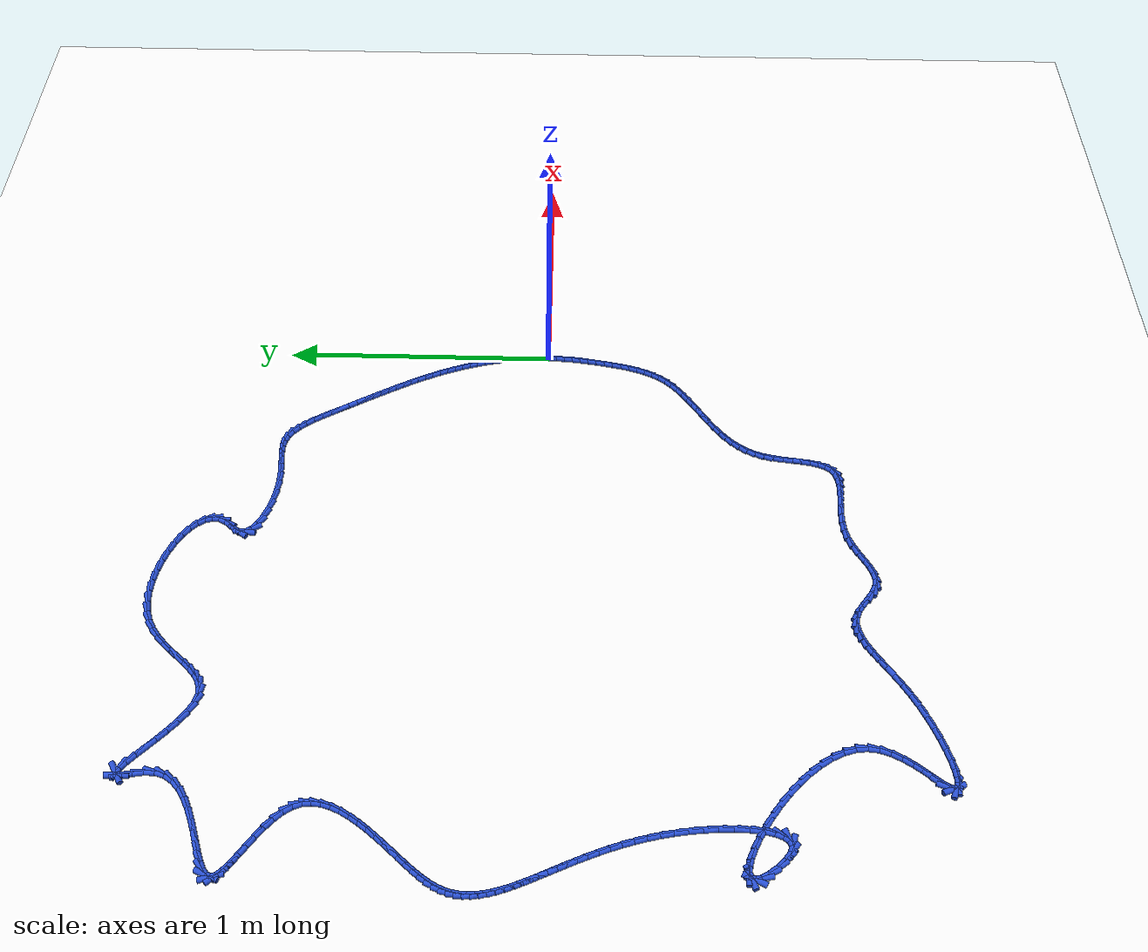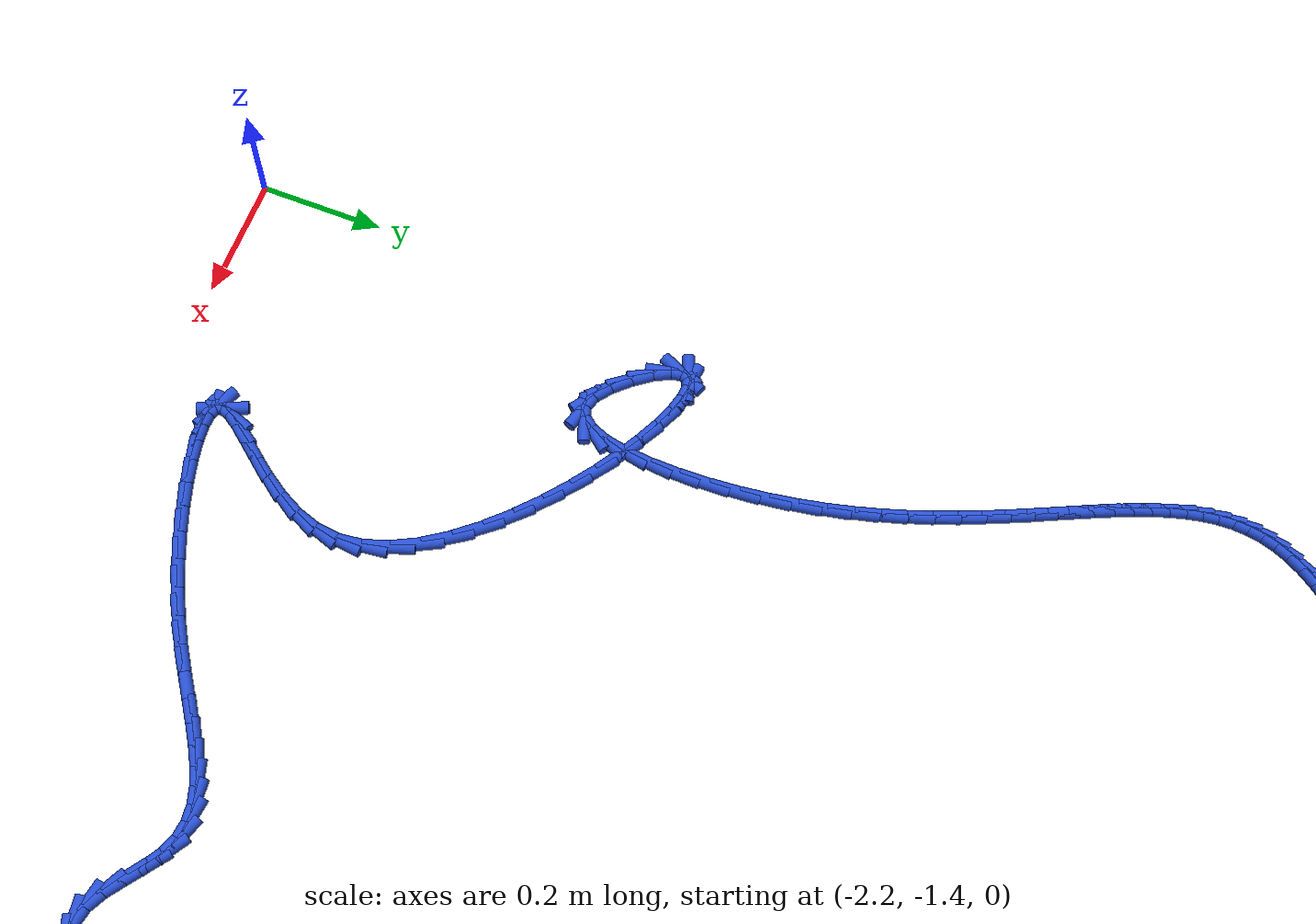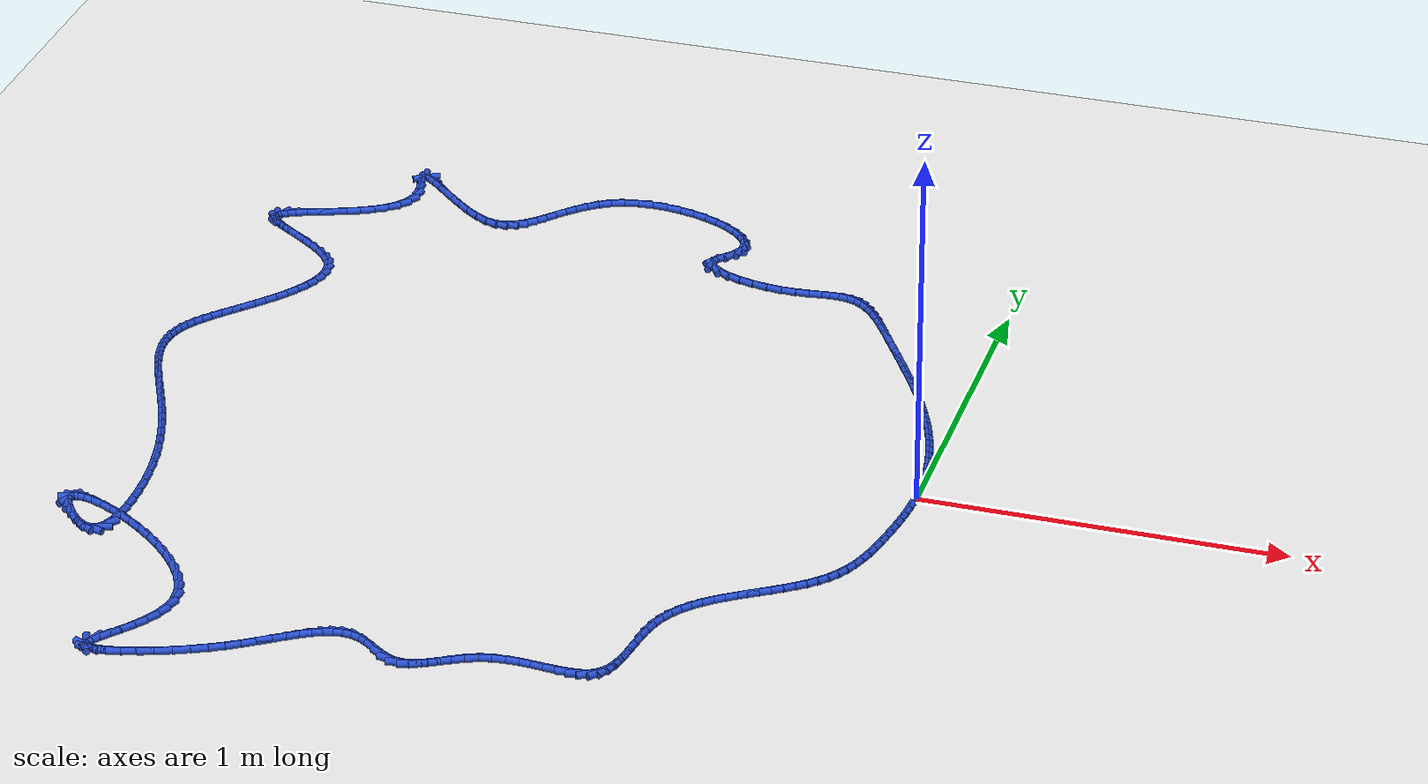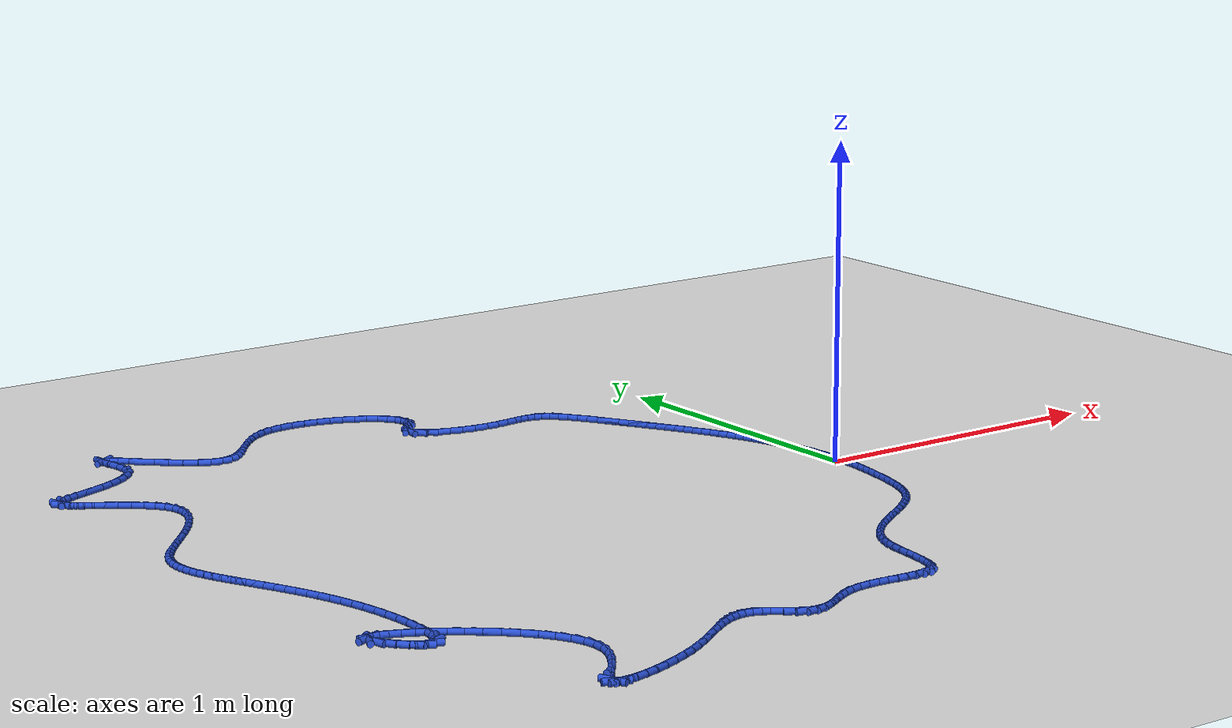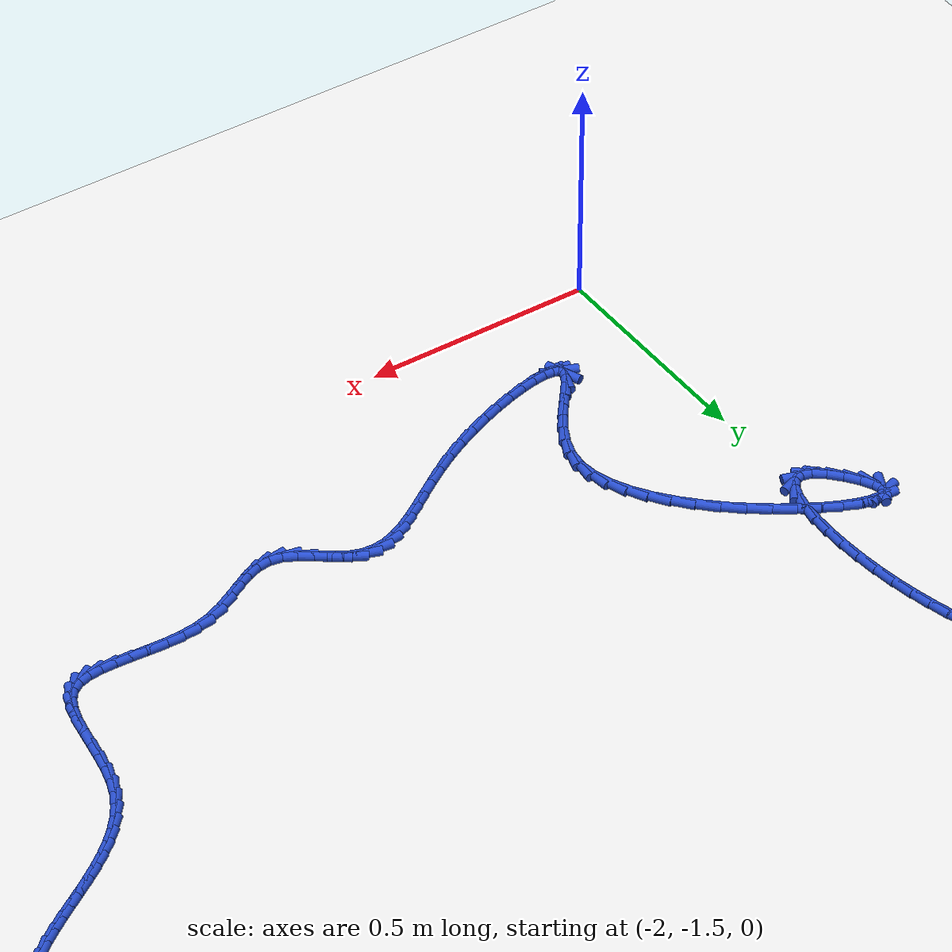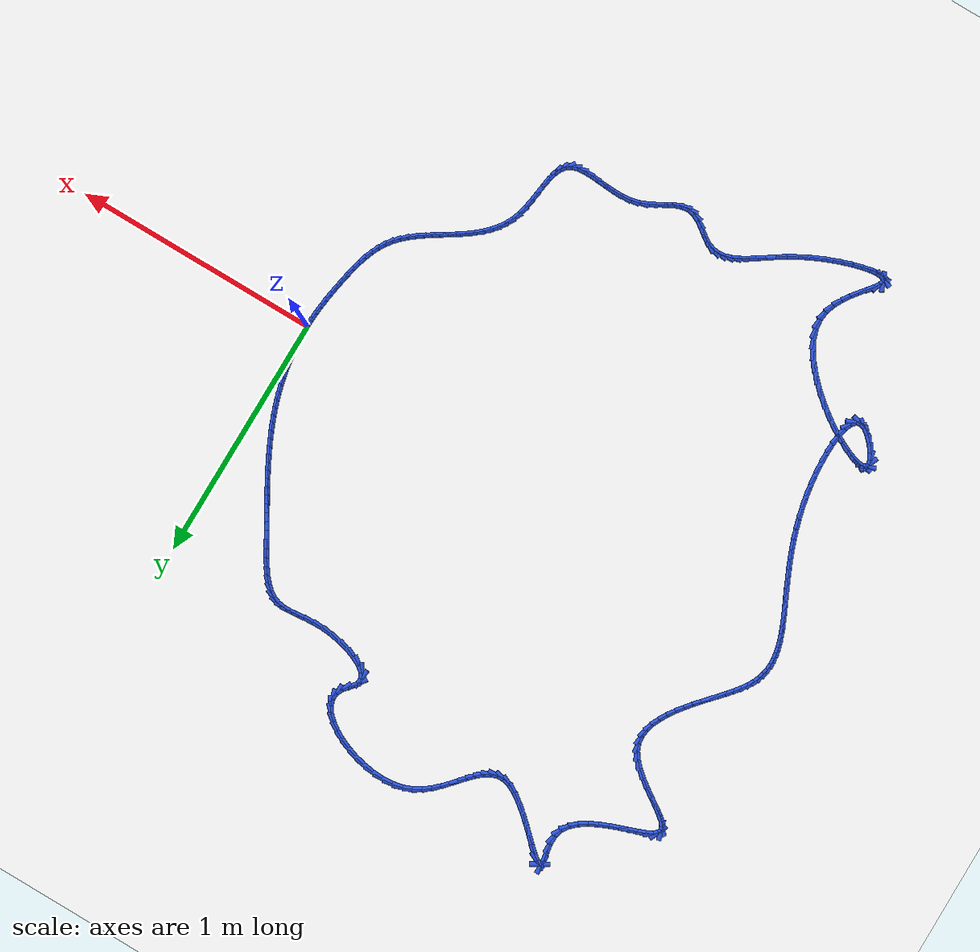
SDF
<sdf version="1.6">
 <world name="default">
  <light name="sun" type="directional">
   <pose>0 0 10 0 -0 0</pose>
   <diffuse>0.8 0.8 0.8 1</diffuse>
   <specular>0.2 0.2 0.2 1</specular>
   <attenuation>
    <range>1000</range>
    <constant>0.9</constant>
    <linear>0.01</linear>
    <quadratic>0.001</quadratic>
   </attenuation>
   <direction>-0.5 0.1 -0.9</direction>
  </light>
  <model name="ground_plane">
   <static>1</static>
   <link name="link">
    <collision name="collision">
     <geometry><plane><normal>0 0 1</normal><size>100 100</size></plane></geometry>
     <surface><friction><ode><mu>100</mu><mu2>50</mu2></ode></friction></surface>
    </collision>
    <visual name="visual">
     <cast_shadows>0</cast_shadows>
     <geometry><plane><normal>0 0 1</normal><size>100 100</size></plane></geometry>
     <material>
      <script><uri>file://media/materials/scripts/gazebo.material</uri><name>Gazebo/WhiteGlow</name></script>
     </material>
    </visual>
   </link>
  </model>
  <gravity>0 0 -9.8</gravity>
  <magnetic_field>6e-06 2.3e-05 -4.2e-05</magnetic_field>
  <atmosphere type="adiabatic"/>
  <physics name="default_physics" default="0" type="ode">
   <max_step_size>0.001</max_step_size>
   <real_time_factor>1</real_time_factor>
   <real_time_update_rate>1000</real_time_update_rate>
  </physics>
  <scene><ambient>0.4 0.4 0.4 1</ambient><background>0.7 0.7 0.7 1</background><shadows>1</shadows></scene>
  <spherical_coordinates>
   <surface_model>EARTH_WGS84</surface_model>
   <latitude_deg>0</latitude_deg>
   <longitude_deg>0</longitude_deg>
   <elevation>0</elevation>
   <heading_deg>0</heading_deg>
  </spherical_coordinates>
  <model name="line">
   <link name="link_0">
    <pose>-7.806255641895632e-18 4.85722573273506e-17 0.01 0 1.57 -1.5604413219199995</pose>
    <collision name="collision">
     <geometry><cylinder><radius>0.01</radius><length>0.08</length></cylinder></geometry>
    </collision>
    <visual name="visual">
     <material>
      <script><name>Gazebo/Blue</name><uri>file://media/materials/scripts/gazebo.material</uri></script>
     </material>
     <geometry><cylinder><radius>0.01</radius><length>0.08</length></cylinder></geometry>
    </visual>
   </link>
   <link name="link_1">
    <pose>-0.0003257807725844156 0.031460065192326254 0.01 0 1.57 -1.525371229036069</pose>
    <collision name="collision">
     <geometry><cylinder><radius>0.01</radius><length>0.08</length></cylinder></geometry>
    </collision>
    <visual name="visual">
     <material>
      <script><name>Gazebo/Blue</name><uri>file://media/materials/scripts/gazebo.material</uri></script>
     </material>
     <geometry><cylinder><radius>0.01</radius><length>0.08</length></cylinder></geometry>
    </visual>
   </link>
   <link name="link_2">
    <pose>-0.001760066610713048 0.06301308879430077 0.01 0 1.57 -1.4916071398277913</pose>
    <collision name="collision">
     <geometry><cylinder><radius>0.01</radius><length>0.08</length></cylinder></geometry>
    </collision>
    <visual name="visual">
     <material>
      <script><name>Gazebo/Blue</name><uri>file://media/materials/scripts/gazebo.material</uri></script>
     </material>
     <geometry><cylinder><radius>0.01</radius><length>0.08</length></cylinder></geometry>
    </visual>
   </link>
   <link name="link_3">
    <pose>-0.0042631440131820604 0.09455581708767911 0.01 0 1.57 -1.4588813321798684</pose>
    <collision name="collision">
     <geometry><cylinder><radius>0.01</radius><length>0.08</length></cylinder></geometry>
    </collision>
    <visual name="visual">
     <material>
      <script><name>Gazebo/Blue</name><uri>file://media/materials/scripts/gazebo.material</uri></script>
     </material>
     <geometry><cylinder><radius>0.01</radius><length>0.08</length></cylinder></geometry>
    </visual>
   </link>
   <link name="link_4">
    <pose>-0.007795299478787609 0.12598499635421676 0.01 0 1.57 -1.4269340386513092</pose>
    <collision name="collision">
     <geometry><cylinder><radius>0.01</radius><length>0.08</length></cylinder></geometry>
    </collision>
    <visual name="visual">
     <material>
      <script><name>Gazebo/Blue</name><uri>file://media/materials/scripts/gazebo.material</uri></script>
     </material>
     <geometry><cylinder><radius>0.01</radius><length>0.08</length></cylinder></geometry>
    </visual>
   </link>
   <link name="link_5">
    <pose>-0.01231681950632586 0.15719737287566926 0.01 0 1.57 -1.3955093590211098</pose>
    <collision name="collision">
     <geometry><cylinder><radius>0.01</radius><length>0.08</length></cylinder></geometry>
    </collision>
    <visual name="visual">
     <material>
      <script><name>Gazebo/Blue</name><uri>file://media/materials/scripts/gazebo.material</uri></script>
     </material>
     <geometry><cylinder><radius>0.01</radius><length>0.08</length></cylinder></geometry>
    </visual>
   </link>
   <link name="link_6">
    <pose>-0.01778799059459297 0.1880896929337921 0.01 0 1.57 -1.364350625744347</pose>
    <collision name="collision">
     <geometry><cylinder><radius>0.01</radius><length>0.08</length></cylinder></geometry>
    </collision>
    <visual name="visual">
     <material>
      <script><name>Gazebo/Blue</name><uri>file://media/materials/scripts/gazebo.material</uri></script>
     </material>
     <geometry><cylinder><radius>0.01</radius><length>0.08</length></cylinder></geometry>
    </visual>
   </link>
   <link name="link_7">
    <pose>-0.024169099242385098 0.21855870281034084 0.01 0 1.57 -1.333301041023382</pose>
    <collision name="collision">
     <geometry><cylinder><radius>0.01</radius><length>0.08</length></cylinder></geometry>
    </collision>
    <visual name="visual">
     <material>
      <script><name>Gazebo/Blue</name><uri>file://media/materials/scripts/gazebo.material</uri></script>
     </material>
     <geometry><cylinder><radius>0.01</radius><length>0.08</length></cylinder></geometry>
    </visual>
   </link>
   <link name="link_8">
    <pose>-0.031421249575513316 0.2485183910856722 0.01 0 1.57 -1.302880161230077</pose>
    <collision name="collision">
     <geometry><cylinder><radius>0.01</radius><length>0.08</length></cylinder></geometry>
    </collision>
    <visual name="visual">
     <material>
      <script><name>Gazebo/Blue</name><uri>file://media/materials/scripts/gazebo.material</uri></script>
     </material>
     <geometry><cylinder><radius>0.01</radius><length>0.08</length></cylinder></geometry>
    </visual>
   </link>
   <link name="link_9">
    <pose>-0.03951041335994463 0.27798539620802065 0.01 0 1.57 -1.2734934558976863</pose>
    <collision name="collision">
     <geometry><cylinder><radius>0.01</radius><length>0.08</length></cylinder></geometry>
    </collision>
    <visual name="visual">
     <material>
      <script><name>Gazebo/Blue</name><uri>file://media/materials/scripts/gazebo.material</uri></script>
     </material>
     <geometry><cylinder><radius>0.01</radius><length>0.08</length></cylinder></geometry>
    </visual>
   </link>
   <link name="link_10">
    <pose>-0.04840435638800448 0.30701418944866293 0.01 0 1.57 -1.2453391597928292</pose>
    <collision name="collision">
     <geometry><cylinder><radius>0.01</radius><length>0.08</length></cylinder></geometry>
    </collision>
    <visual name="visual">
     <material>
      <script><name>Gazebo/Blue</name><uri>file://media/materials/scripts/gazebo.material</uri></script>
     </material>
     <geometry><cylinder><radius>0.01</radius><length>0.08</length></cylinder></geometry>
    </visual>
   </link>
   <link name="link_11">
    <pose>-0.05807084727160707 0.3356593015389859 0.01 0 1.57 -1.2185956438059296</pose>
    <collision name="collision">
     <geometry><cylinder><radius>0.01</radius><length>0.08</length></cylinder></geometry>
    </collision>
    <visual name="visual">
     <material>
      <script><name>Gazebo/Blue</name><uri>file://media/materials/scripts/gazebo.material</uri></script>
     </material>
     <geometry><cylinder><radius>0.01</radius><length>0.08</length></cylinder></geometry>
    </visual>
   </link>
   <link name="link_12">
    <pose>-0.06847765462266663 0.3639752632103765 0.01 0 1.57 -1.1934186810547682</pose>
    <collision name="collision">
     <geometry><cylinder><radius>0.01</radius><length>0.08</length></cylinder></geometry>
    </collision>
    <visual name="visual">
     <material>
      <script><name>Gazebo/Blue</name><uri>file://media/materials/scripts/gazebo.material</uri></script>
     </material>
     <geometry><cylinder><radius>0.01</radius><length>0.08</length></cylinder></geometry>
    </visual>
   </link>
   <link name="link_13">
    <pose>-0.07959254705309736 0.39201660519422166 0.01 0 1.57 -1.1699395097360588</pose>
    <collision name="collision">
     <geometry><cylinder><radius>0.01</radius><length>0.08</length></cylinder></geometry>
    </collision>
    <visual name="visual">
     <material>
      <script><name>Gazebo/Blue</name><uri>file://media/materials/scripts/gazebo.material</uri></script>
     </material>
     <geometry><cylinder><radius>0.01</radius><length>0.08</length></cylinder></geometry>
    </visual>
   </link>
   <link name="link_14">
    <pose>-0.09138329317481346 0.41983785822190833 0.01 0 1.57 -1.1482640205944987</pose>
    <collision name="collision">
     <geometry><cylinder><radius>0.01</radius><length>0.08</length></cylinder></geometry>
    </collision>
    <visual name="visual">
     <material>
      <script><name>Gazebo/Blue</name><uri>file://media/materials/scripts/gazebo.material</uri></script>
     </material>
     <geometry><cylinder><radius>0.01</radius><length>0.08</length></cylinder></geometry>
    </visual>
   </link>
   <link name="link_15">
    <pose>-0.1038176615997292 0.4474935530248233 0.01 0 1.57 -1.128472947034182</pose>
    <collision name="collision">
     <geometry><cylinder><radius>0.01</radius><length>0.08</length></cylinder></geometry>
    </collision>
    <visual name="visual">
     <material>
      <script><name>Gazebo/Blue</name><uri>file://media/materials/scripts/gazebo.material</uri></script>
     </material>
     <geometry><cylinder><radius>0.01</radius><length>0.08</length></cylinder></geometry>
    </visual>
   </link>
   <link name="link_16">
    <pose>-0.11686342093975881 0.4750382203343537 0.01 0 1.57 -1.110622879269722</pose>
    <collision name="collision">
     <geometry><cylinder><radius>0.01</radius><length>0.08</length></cylinder></geometry>
    </collision>
    <visual name="visual">
     <material>
      <script><name>Gazebo/Blue</name><uri>file://media/materials/scripts/gazebo.material</uri></script>
     </material>
     <geometry><cylinder><radius>0.01</radius><length>0.08</length></cylinder></geometry>
    </visual>
   </link>
   <link name="link_17">
    <pose>-0.13048833980681648 0.5025263908818863 0.01 0 1.57 -1.0947478968333602</pose>
    <collision name="collision">
     <geometry><cylinder><radius>0.01</radius><length>0.08</length></cylinder></geometry>
    </collision>
    <visual name="visual">
     <material>
      <script><name>Gazebo/Blue</name><uri>file://media/materials/scripts/gazebo.material</uri></script>
     </material>
     <geometry><cylinder><radius>0.01</radius><length>0.08</length></cylinder></geometry>
    </visual>
   </link>
   <link name="link_18">
    <pose>-0.1446601868128164 0.530012595398808 0.01 0 1.57 -1.080861612639124</pose>
    <collision name="collision">
     <geometry><cylinder><radius>0.01</radius><length>0.08</length></cylinder></geometry>
    </collision>
    <visual name="visual">
     <material>
      <script><name>Gazebo/Blue</name><uri>file://media/materials/scripts/gazebo.material</uri></script>
     </material>
     <geometry><cylinder><radius>0.01</radius><length>0.08</length></cylinder></geometry>
    </visual>
   </link>
   <link name="link_19">
    <pose>-0.15934673056967286 0.557551364616506 0.01 0 1.57 -1.0689594402174178</pose>
    <collision name="collision">
     <geometry><cylinder><radius>0.01</radius><length>0.08</length></cylinder></geometry>
    </collision>
    <visual name="visual">
     <material>
      <script><name>Gazebo/Blue</name><uri>file://media/materials/scripts/gazebo.material</uri></script>
     </material>
     <geometry><cylinder><radius>0.01</radius><length>0.08</length></cylinder></geometry>
    </visual>
   </link>
   <link name="link_20">
    <pose>-0.17451573968930006 0.5851972292663671 0.01 0 1.57 -1.0590209263301715</pose>
    <collision name="collision">
     <geometry><cylinder><radius>0.01</radius><length>0.08</length></cylinder></geometry>
    </collision>
    <visual name="visual">
     <material>
      <script><name>Gazebo/Blue</name><uri>file://media/materials/scripts/gazebo.material</uri></script>
     </material>
     <geometry><cylinder><radius>0.01</radius><length>0.08</length></cylinder></geometry>
    </visual>
   </link>
   <link name="link_21">
    <pose>-0.19013498278361216 0.6130047200797778 0.01 0 1.57 -1.0510120272003123</pose>
    <collision name="collision">
     <geometry><cylinder><radius>0.01</radius><length>0.08</length></cylinder></geometry>
    </collision>
    <visual name="visual">
     <material>
      <script><name>Gazebo/Blue</name><uri>file://media/materials/scripts/gazebo.material</uri></script>
     </material>
     <geometry><cylinder><radius>0.01</radius><length>0.08</length></cylinder></geometry>
    </visual>
   </link>
   <link name="link_22">
    <pose>-0.2061722284645235 0.6410283677881257 0.01 0 1.57 -1.0448872427274944</pose>
    <collision name="collision">
     <geometry><cylinder><radius>0.01</radius><length>0.08</length></cylinder></geometry>
    </collision>
    <visual name="visual">
     <material>
      <script><name>Gazebo/Blue</name><uri>file://media/materials/scripts/gazebo.material</uri></script>
     </material>
     <geometry><cylinder><radius>0.01</radius><length>0.08</length></cylinder></geometry>
    </visual>
   </link>
   <link name="link_23">
    <pose>-0.2225952453439482 0.6693227031227972 0.01 0 1.57 -1.0405915557319558</pose>
    <collision name="collision">
     <geometry><cylinder><radius>0.01</radius><length>0.08</length></cylinder></geometry>
    </collision>
    <visual name="visual">
     <material>
      <script><name>Gazebo/Blue</name><uri>file://media/materials/scripts/gazebo.material</uri></script>
     </material>
     <geometry><cylinder><radius>0.01</radius><length>0.08</length></cylinder></geometry>
    </visual>
   </link>
   <link name="link_24">
    <pose>-0.23937180203380048 0.6979422568151794 0.01 0 1.57 -1.038062150497498</pose>
    <collision name="collision">
     <geometry><cylinder><radius>0.01</radius><length>0.08</length></cylinder></geometry>
    </collision>
    <visual name="visual">
     <material>
      <script><name>Gazebo/Blue</name><uri>file://media/materials/scripts/gazebo.material</uri></script>
     </material>
     <geometry><cylinder><radius>0.01</radius><length>0.08</length></cylinder></geometry>
    </visual>
   </link>
   <link name="link_25">
    <pose>-0.2564696671459946 0.7269415595966595 0.01 0 1.57 -1.0372299059757648</pose>
    <collision name="collision">
     <geometry><cylinder><radius>0.01</radius><length>0.08</length></cylinder></geometry>
    </collision>
    <visual name="visual">
     <material>
      <script><name>Gazebo/Blue</name><uri>file://media/materials/scripts/gazebo.material</uri></script>
     </material>
     <geometry><cylinder><radius>0.01</radius><length>0.08</length></cylinder></geometry>
    </visual>
   </link>
   <link name="link_26">
    <pose>-0.2738566092924449 0.7563751421986242 0.01 0 1.57 -1.0380206741448013</pose>
    <collision name="collision">
     <geometry><cylinder><radius>0.01</radius><length>0.08</length></cylinder></geometry>
    </collision>
    <visual name="visual">
     <material>
      <script><name>Gazebo/Blue</name><uri>file://media/materials/scripts/gazebo.material</uri></script>
     </material>
     <geometry><cylinder><radius>0.01</radius><length>0.08</length></cylinder></geometry>
    </visual>
   </link>
   <link name="link_27">
    <pose>-0.2915003970850653 0.7862975353524602 0.01 0 1.57 -1.037987114227847</pose>
    <collision name="collision">
     <geometry><cylinder><radius>0.01</radius><length>0.08</length></cylinder></geometry>
    </collision>
    <visual name="visual">
     <material>
      <script><name>Gazebo/Blue</name><uri>file://media/materials/scripts/gazebo.material</uri></script>
     </material>
     <geometry><cylinder><radius>0.01</radius><length>0.08</length></cylinder></geometry>
    </visual>
   </link>
   <link name="link_28">
    <pose>-0.3093941555290255 0.816641530355099 0.01 0 1.57 -1.0244099191906808</pose>
    <collision name="collision">
     <geometry><cylinder><radius>0.01</radius><length>0.08</length></cylinder></geometry>
    </collision>
    <visual name="visual">
     <material>
      <script><name>Gazebo/Blue</name><uri>file://media/materials/scripts/gazebo.material</uri></script>
     </material>
     <geometry><cylinder><radius>0.01</radius><length>0.08</length></cylinder></geometry>
    </visual>
   </link>
   <link name="link_29">
    <pose>-0.32766678098147045 0.8466880620884716 0.01 0 1.57 -0.9920492674054355</pose>
    <collision name="collision">
     <geometry><cylinder><radius>0.01</radius><length>0.08</length></cylinder></geometry>
    </collision>
    <visual name="visual">
     <material>
      <script><name>Gazebo/Blue</name><uri>file://media/materials/scripts/gazebo.material</uri></script>
     </material>
     <geometry><cylinder><radius>0.01</radius><length>0.08</length></cylinder></geometry>
    </visual>
   </link>
   <link name="link_30">
    <pose>-0.34649242289709453 0.8755007992623202 0.01 0 1.57 -0.9376806537002139</pose>
    <collision name="collision">
     <geometry><cylinder><radius>0.01</radius><length>0.08</length></cylinder></geometry>
    </collision>
    <visual name="visual">
     <material>
      <script><name>Gazebo/Blue</name><uri>file://media/materials/scripts/gazebo.material</uri></script>
     </material>
     <geometry><cylinder><radius>0.01</radius><length>0.08</length></cylinder></geometry>
    </visual>
   </link>
   <link name="link_31">
    <pose>-0.3660452618326739 0.9021432612611355 0.01 0 1.57 -0.8553338217312091</pose>
    <collision name="collision">
     <geometry><cylinder><radius>0.01</radius><length>0.08</length></cylinder></geometry>
    </collision>
    <visual name="visual">
     <material>
      <script><name>Gazebo/Blue</name><uri>file://media/materials/scripts/gazebo.material</uri></script>
     </material>
     <geometry><cylinder><radius>0.01</radius><length>0.08</length></cylinder></geometry>
    </visual>
   </link>
   <link name="link_32">
    <pose>-0.3864994783449847 0.9256789674694083 0.01 0 1.57 -0.7357755166653023</pose>
    <collision name="collision">
     <geometry><cylinder><radius>0.01</radius><length>0.08</length></cylinder></geometry>
    </collision>
    <visual name="visual">
     <material>
      <script><name>Gazebo/Blue</name><uri>file://media/materials/scripts/gazebo.material</uri></script>
     </material>
     <geometry><cylinder><radius>0.01</radius><length>0.08</length></cylinder></geometry>
    </visual>
   </link>
   <link name="link_33">
    <pose>-0.4080292529908031 0.9451714372716283 0.01 0 1.57 -0.5672508133186392</pose>
    <collision name="collision">
     <geometry><cylinder><radius>0.01</radius><length>0.08</length></cylinder></geometry>
    </collision>
    <visual name="visual">
     <material>
      <script><name>Gazebo/Blue</name><uri>file://media/materials/scripts/gazebo.material</uri></script>
     </material>
     <geometry><cylinder><radius>0.01</radius><length>0.08</length></cylinder></geometry>
    </visual>
   </link>
   <link name="link_34">
    <pose>-0.43080876632690523 0.9596841900522866 0.01 0 1.57 -0.3464986876725425</pose>
    <collision name="collision">
     <geometry><cylinder><radius>0.01</radius><length>0.08</length></cylinder></geometry>
    </collision>
    <visual name="visual">
     <material>
      <script><name>Gazebo/Blue</name><uri>file://media/materials/scripts/gazebo.material</uri></script>
     </material>
     <geometry><cylinder><radius>0.01</radius><length>0.08</length></cylinder></geometry>
    </visual>
   </link>
   <link name="link_35">
    <pose>-0.455017104530727 0.9684249905326571 0.01 0 1.57 -0.13820005782777642</pose>
    <collision name="collision">
     <geometry><cylinder><radius>0.01</radius><length>0.08</length></cylinder></geometry>
    </collision>
    <visual name="visual">
     <material>
      <script><name>Gazebo/Blue</name><uri>file://media/materials/scripts/gazebo.material</uri></script>
     </material>
     <geometry><cylinder><radius>0.01</radius><length>0.08</length></cylinder></geometry>
    </visual>
   </link>
   <link name="link_36">
    <pose>-0.48088167371348317 0.9720224073657954 0.01 0 1.57 0.003934838977855753</pose>
    <collision name="collision">
     <geometry><cylinder><radius>0.01</radius><length>0.08</length></cylinder></geometry>
    </collision>
    <visual name="visual">
     <material>
      <script><name>Gazebo/Blue</name><uri>file://media/materials/scripts/gazebo.material</uri></script>
     </material>
     <geometry><cylinder><radius>0.01</radius><length>0.08</length></cylinder></geometry>
    </visual>
   </link>
   <link name="link_37">
    <pose>-0.5086573627138247 0.9719131139380176 0.01 0 1.57 0.07898812055758157</pose>
    <collision name="collision">
     <geometry><cylinder><radius>0.01</radius><length>0.08</length></cylinder></geometry>
    </collision>
    <visual name="visual">
     <material>
      <script><name>Gazebo/Blue</name><uri>file://media/materials/scripts/gazebo.material</uri></script>
     </material>
     <geometry><cylinder><radius>0.01</radius><length>0.08</length></cylinder></geometry>
    </visual>
   </link>
   <link name="link_38">
    <pose>-0.5385993778721694 0.9695431194878243 0.01 0 1.57 0.09808770693141301</pose>
    <collision name="collision">
     <geometry><cylinder><radius>0.01</radius><length>0.08</length></cylinder></geometry>
    </collision>
    <visual name="visual">
     <material>
      <script><name>Gazebo/Blue</name><uri>file://media/materials/scripts/gazebo.material</uri></script>
     </material>
     <geometry><cylinder><radius>0.01</radius><length>0.08</length></cylinder></geometry>
    </visual>
   </link>
   <link name="link_39">
    <pose>-0.570962925528936 0.9663584332537161 0.01 0 1.57 0.07274094890611618</pose>
    <collision name="collision">
     <geometry><cylinder><radius>0.01</radius><length>0.08</length></cylinder></geometry>
    </collision>
    <visual name="visual">
     <material>
      <script><name>Gazebo/Blue</name><uri>file://media/materials/scripts/gazebo.material</uri></script>
     </material>
     <geometry><cylinder><radius>0.01</radius><length>0.08</length></cylinder></geometry>
    </visual>
   </link>
   <link name="link_40">
    <pose>-0.6060032120245422 0.9638050644741935 0.01 0 1.57 0.012535927665842815</pose>
    <collision name="collision">
     <geometry><cylinder><radius>0.01</radius><length>0.08</length></cylinder></geometry>
    </collision>
    <visual name="visual">
     <material>
      <script><name>Gazebo/Blue</name><uri>file://media/materials/scripts/gazebo.material</uri></script>
     </material>
     <geometry><cylinder><radius>0.01</radius><length>0.08</length></cylinder></geometry>
    </visual>
   </link>
   <link name="link_41">
    <pose>-0.6439754436994063 0.9633290223877563 0.01 0 1.57 -0.073056312298346</pose>
    <collision name="collision">
     <geometry><cylinder><radius>0.01</radius><length>0.08</length></cylinder></geometry>
    </collision>
    <visual name="visual">
     <material>
      <script><name>Gazebo/Blue</name><uri>file://media/materials/scripts/gazebo.material</uri></script>
     </material>
     <geometry><cylinder><radius>0.01</radius><length>0.08</length></cylinder></geometry>
    </visual>
   </link>
   <link name="link_42">
    <pose>-0.6850713372633097 0.9663366895923248 0.01 0 1.57 -0.16156675859563335</pose>
    <collision name="collision">
     <geometry><cylinder><radius>0.01</radius><length>0.08</length></cylinder></geometry>
    </collision>
    <visual name="visual">
     <material>
      <script><name>Gazebo/Blue</name><uri>file://media/materials/scripts/gazebo.material</uri></script>
     </material>
     <geometry><cylinder><radius>0.01</radius><length>0.08</length></cylinder></geometry>
    </visual>
   </link>
   <link name="link_43">
    <pose>-0.7280529850939443 0.9733421579447216 0.01 0 1.57 -0.246792449291581</pose>
    <collision name="collision">
     <geometry><cylinder><radius>0.01</radius><length>0.08</length></cylinder></geometry>
    </collision>
    <visual name="visual">
     <material>
      <script><name>Gazebo/Blue</name><uri>file://media/materials/scripts/gazebo.material</uri></script>
     </material>
     <geometry><cylinder><radius>0.01</radius><length>0.08</length></cylinder></geometry>
    </visual>
   </link>
   <link name="link_44">
    <pose>-0.77026967154288 0.9839777243488143 0.01 0 1.57 -0.343582504696271</pose>
    <collision name="collision">
     <geometry><cylinder><radius>0.01</radius><length>0.08</length></cylinder></geometry>
    </collision>
    <visual name="visual">
     <material>
      <script><name>Gazebo/Blue</name><uri>file://media/materials/scripts/gazebo.material</uri></script>
     </material>
     <geometry><cylinder><radius>0.01</radius><length>0.08</length></cylinder></geometry>
    </visual>
   </link>
   <link name="link_45">
    <pose>-0.8090105547398543 0.9978381583176504 0.01 0 1.57 -0.47350079707516657</pose>
    <collision name="collision">
     <geometry><cylinder><radius>0.01</radius><length>0.08</length></cylinder></geometry>
    </collision>
    <visual name="visual">
     <material>
      <script><name>Gazebo/Blue</name><uri>file://media/materials/scripts/gazebo.material</uri></script>
     </material>
     <geometry><cylinder><radius>0.01</radius><length>0.08</length></cylinder></geometry>
    </visual>
   </link>
   <link name="link_46">
    <pose>-0.8415647928146066 1.014518229364278 0.01 0 1.57 -0.6790837517820342</pose>
    <collision name="collision">
     <geometry><cylinder><radius>0.01</radius><length>0.08</length></cylinder></geometry>
    </collision>
    <visual name="visual">
     <material>
      <script><name>Gazebo/Blue</name><uri>file://media/materials/scripts/gazebo.material</uri></script>
     </material>
     <geometry><cylinder><radius>0.01</radius><length>0.08</length></cylinder></geometry>
    </visual>
   </link>
   <link name="link_47">
    <pose>-0.8652215438968757 1.033612707001745 0.01 0 1.57 -1.052036389093886</pose>
    <collision name="collision">
     <geometry><cylinder><radius>0.01</radius><length>0.08</length></cylinder></geometry>
    </collision>
    <visual name="visual">
     <material>
      <script><name>Gazebo/Blue</name><uri>file://media/materials/scripts/gazebo.material</uri></script>
     </material>
     <geometry><cylinder><radius>0.01</radius><length>0.08</length></cylinder></geometry>
    </visual>
   </link>
   <link name="link_48">
    <pose>-0.8772699661163998 1.0547163607430983 0.01 0 1.57 1.4711281723420833</pose>
    <collision name="collision">
     <geometry><cylinder><radius>0.01</radius><length>0.08</length></cylinder></geometry>
    </collision>
    <visual name="visual">
     <material>
      <script><name>Gazebo/Blue</name><uri>file://media/materials/scripts/gazebo.material</uri></script>
     </material>
     <geometry><cylinder><radius>0.01</radius><length>0.08</length></cylinder></geometry>
    </visual>
   </link>
   <link name="link_49">
    <pose>-0.8749992176029183 1.0774239601013862 0.01 0 1.57 0.945119175996891</pose>
    <collision name="collision">
     <geometry><cylinder><radius>0.01</radius><length>0.08</length></cylinder></geometry>
    </collision>
    <visual name="visual">
     <material>
      <script><name>Gazebo/Blue</name><uri>file://media/materials/scripts/gazebo.material</uri></script>
     </material>
     <geometry><cylinder><radius>0.01</radius><length>0.08</length></cylinder></geometry>
    </visual>
   </link>
   <link name="link_50">
    <pose>-0.8577183418856522 1.101341644554557 0.01 0 1.57 0.8644308224118262</pose>
    <collision name="collision">
     <geometry><cylinder><radius>0.01</radius><length>0.08</length></cylinder></geometry>
    </collision>
    <visual name="visual">
     <material>
      <script><name>Gazebo/Blue</name><uri>file://media/materials/scripts/gazebo.material</uri></script>
     </material>
     <geometry><cylinder><radius>0.01</radius><length>0.08</length></cylinder></geometry>
    </visual>
   </link>
   <link name="link_51">
    <pose>-0.8365578842101027 1.1261420969892197 0.01 0 1.57 1.1188612966358709</pose>
    <collision name="collision">
     <geometry><cylinder><radius>0.01</radius><length>0.08</length></cylinder></geometry>
    </collision>
    <visual name="visual">
     <material>
      <script><name>Gazebo/Blue</name><uri>file://media/materials/scripts/gazebo.material</uri></script>
     </material>
     <geometry><cylinder><radius>0.01</radius><length>0.08</length></cylinder></geometry>
    </visual>
   </link>
   <link name="link_52">
    <pose>-0.8242489779260815 1.1514980802542776 0.01 0 1.57 1.5028957018875282</pose>
    <collision name="collision">
     <geometry><cylinder><radius>0.01</radius><length>0.08</length></cylinder></geometry>
    </collision>
    <visual name="visual">
     <material>
      <script><name>Gazebo/Blue</name><uri>file://media/materials/scripts/gazebo.material</uri></script>
     </material>
     <geometry><cylinder><radius>0.01</radius><length>0.08</length></cylinder></geometry>
    </visual>
   </link>
   <link name="link_53">
    <pose>-0.8225158171109846 1.1769838018077912 0.01 0 1.57 -1.2721895305204625</pose>
    <collision name="collision">
     <geometry><cylinder><radius>0.01</radius><length>0.08</length></cylinder></geometry>
    </collision>
    <visual name="visual">
     <material>
      <script><name>Gazebo/Blue</name><uri>file://media/materials/scripts/gazebo.material</uri></script>
     </material>
     <geometry><cylinder><radius>0.01</radius><length>0.08</length></cylinder></geometry>
    </visual>
   </link>
   <link name="link_54">
    <pose>-0.8302616852094674 1.2021482159791834 0.01 0 1.57 -0.9865836661304525</pose>
    <collision name="collision">
     <geometry><cylinder><radius>0.01</radius><length>0.08</length></cylinder></geometry>
    </collision>
    <visual name="visual">
     <material>
      <script><name>Gazebo/Blue</name><uri>file://media/materials/scripts/gazebo.material</uri></script>
     </material>
     <geometry><cylinder><radius>0.01</radius><length>0.08</length></cylinder></geometry>
    </visual>
   </link>
   <link name="link_55">
    <pose>-0.8463898642056272 1.226540277084801 0.01 0 1.57 -0.7801363675360878</pose>
    <collision name="collision">
     <geometry><cylinder><radius>0.01</radius><length>0.08</length></cylinder></geometry>
    </collision>
    <visual name="visual">
     <material>
      <script><name>Gazebo/Blue</name><uri>file://media/materials/scripts/gazebo.material</uri></script>
     </material>
     <geometry><cylinder><radius>0.01</radius><length>0.08</length></cylinder></geometry>
    </visual>
   </link>
   <link name="link_56">
    <pose>-0.86980363608356 1.24970893944099 0.01 0 1.57 -0.6280229946637196</pose>
    <collision name="collision">
     <geometry><cylinder><radius>0.01</radius><length>0.08</length></cylinder></geometry>
    </collision>
    <visual name="visual">
     <material>
      <script><name>Gazebo/Blue</name><uri>file://media/materials/scripts/gazebo.material</uri></script>
     </material>
     <geometry><cylinder><radius>0.01</radius><length>0.08</length></cylinder></geometry>
    </visual>
   </link>
   <link name="link_57">
    <pose>-0.899406282827363 1.271203157364097 0.01 0 1.57 -0.5091628836332616</pose>
    <collision name="collision">
     <geometry><cylinder><radius>0.01</radius><length>0.08</length></cylinder></geometry>
    </collision>
    <visual name="visual">
     <material>
      <script><name>Gazebo/Blue</name><uri>file://media/materials/scripts/gazebo.material</uri></script>
     </material>
     <geometry><cylinder><radius>0.01</radius><length>0.08</length></cylinder></geometry>
    </visual>
   </link>
   <link name="link_58">
    <pose>-0.9341010864211325 1.2905718851704688 0.01 0 1.57 -0.40948259705434087</pose>
    <collision name="collision">
     <geometry><cylinder><radius>0.01</radius><length>0.08</length></cylinder></geometry>
    </collision>
    <visual name="visual">
     <material>
      <script><name>Gazebo/Blue</name><uri>file://media/materials/scripts/gazebo.material</uri></script>
     </material>
     <geometry><cylinder><radius>0.01</radius><length>0.08</length></cylinder></geometry>
    </visual>
   </link>
   <link name="link_59">
    <pose>-0.9727913288489658 1.3073640771764525 0.01 0 1.57 -0.31962012750378194</pose>
    <collision name="collision">
     <geometry><cylinder><radius>0.01</radius><length>0.08</length></cylinder></geometry>
    </collision>
    <visual name="visual">
     <material>
      <script><name>Gazebo/Blue</name><uri>file://media/materials/scripts/gazebo.material</uri></script>
     </material>
     <geometry><cylinder><radius>0.01</radius><length>0.08</length></cylinder></geometry>
    </visual>
   </link>
   <link name="link_60">
    <pose>-1.0143802920949585 1.3211286876983939 0.01 0 1.57 -0.2327571639845759</pose>
    <collision name="collision">
     <geometry><cylinder><radius>0.01</radius><length>0.08</length></cylinder></geometry>
    </collision>
    <visual name="visual">
     <material>
      <script><name>Gazebo/Blue</name><uri>file://media/materials/scripts/gazebo.material</uri></script>
     </material>
     <geometry><cylinder><radius>0.01</radius><length>0.08</length></cylinder></geometry>
    </visual>
   </link>
   <link name="link_61">
    <pose>-1.0577712581432088 1.3314146710526407 0.01 0 1.57 -0.14316017998984593</pose>
    <collision name="collision">
     <geometry><cylinder><radius>0.01</radius><length>0.08</length></cylinder></geometry>
    </collision>
    <visual name="visual">
     <material>
      <script><name>Gazebo/Blue</name><uri>file://media/materials/scripts/gazebo.material</uri></script>
     </material>
     <geometry><cylinder><radius>0.01</radius><length>0.08</length></cylinder></geometry>
    </visual>
   </link>
   <link name="link_62">
    <pose>-1.101867508977812 1.3377709815555383 0.01 0 1.57 -0.0451723204915118</pose>
    <collision name="collision">
     <geometry><cylinder><radius>0.01</radius><length>0.08</length></cylinder></geometry>
    </collision>
    <visual name="visual">
     <material>
      <script><name>Gazebo/Blue</name><uri>file://media/materials/scripts/gazebo.material</uri></script>
     </material>
     <geometry><cylinder><radius>0.01</radius><length>0.08</length></cylinder></geometry>
    </visual>
   </link>
   <link name="link_63">
    <pose>-1.145572326582866 1.339746573523434 0.01 0 1.57 0.06755214605993315</pose>
    <collision name="collision">
     <geometry><cylinder><radius>0.01</radius><length>0.08</length></cylinder></geometry>
    </collision>
    <visual name="visual">
     <material>
      <script><name>Gazebo/Blue</name><uri>file://media/materials/scripts/gazebo.material</uri></script>
     </material>
     <geometry><cylinder><radius>0.01</radius><length>0.08</length></cylinder></geometry>
    </visual>
   </link>
   <link name="link_64">
    <pose>-1.1877889929424663 1.336890401272675 0.01 0 1.57 0.20254880623692054</pose>
    <collision name="collision">
     <geometry><cylinder><radius>0.01</radius><length>0.08</length></cylinder></geometry>
    </collision>
    <visual name="visual">
     <material>
      <script><name>Gazebo/Blue</name><uri>file://media/materials/scripts/gazebo.material</uri></script>
     </material>
     <geometry><cylinder><radius>0.01</radius><length>0.08</length></cylinder></geometry>
    </visual>
   </link>
   <link name="link_65">
    <pose>-1.2274207900407101 1.3287514191196068 0.01 0 1.57 0.3648283171285513</pose>
    <collision name="collision">
     <geometry><cylinder><radius>0.01</radius><length>0.08</length></cylinder></geometry>
    </collision>
    <visual name="visual">
     <material>
      <script><name>Gazebo/Blue</name><uri>file://media/materials/scripts/gazebo.material</uri></script>
     </material>
     <geometry><cylinder><radius>0.01</radius><length>0.08</length></cylinder></geometry>
    </visual>
   </link>
   <link name="link_66">
    <pose>-1.2634730539737098 1.3149821466862484 0.01 0 1.57 0.5236739812597687</pose>
    <collision name="collision">
     <geometry><cylinder><radius>0.01</radius><length>0.08</length></cylinder></geometry>
    </collision>
    <visual name="visual">
     <material>
      <script><name>Gazebo/Blue</name><uri>file://media/materials/scripts/gazebo.material</uri></script>
     </material>
     <geometry><cylinder><radius>0.01</radius><length>0.08</length></cylinder></geometry>
    </visual>
   </link>
   <link name="link_67">
    <pose>-1.29593715188715 1.2962357355636238 0.01 0 1.57 0.6531140520029104</pose>
    <collision name="collision">
     <geometry><cylinder><radius>0.01</radius><length>0.08</length></cylinder></geometry>
    </collision>
    <visual name="visual">
     <material>
      <script><name>Gazebo/Blue</name><uri>file://media/materials/scripts/gazebo.material</uri></script>
     </material>
     <geometry><cylinder><radius>0.01</radius><length>0.08</length></cylinder></geometry>
    </visual>
   </link>
   <link name="link_68">
    <pose>-1.3253568120599895 1.2737258777117726 0.01 0 1.57 0.7494066978372222</pose>
    <collision name="collision">
     <geometry><cylinder><radius>0.01</radius><length>0.08</length></cylinder></geometry>
    </collision>
    <visual name="visual">
     <material>
      <script><name>Gazebo/Blue</name><uri>file://media/materials/scripts/gazebo.material</uri></script>
     </material>
     <geometry><cylinder><radius>0.01</radius><length>0.08</length></cylinder></geometry>
    </visual>
   </link>
   <link name="link_69">
    <pose>-1.3522818435271449 1.2486724358891201 0.01 0 1.57 0.8125920547162688</pose>
    <collision name="collision">
     <geometry><cylinder><radius>0.01</radius><length>0.08</length></cylinder></geometry>
    </collision>
    <visual name="visual">
     <material>
      <script><name>Gazebo/Blue</name><uri>file://media/materials/scripts/gazebo.material</uri></script>
     </material>
     <geometry><cylinder><radius>0.01</radius><length>0.08</length></cylinder></geometry>
    </visual>
   </link>
   <link name="link_70">
    <pose>-1.377262055323533 1.222295272854091 0.01 0 1.57 0.8431735931201993</pose>
    <collision name="collision">
     <geometry><cylinder><radius>0.01</radius><length>0.08</length></cylinder></geometry>
    </collision>
    <visual name="visual">
     <material>
      <script><name>Gazebo/Blue</name><uri>file://media/materials/scripts/gazebo.material</uri></script>
     </material>
     <geometry><cylinder><radius>0.01</radius><length>0.08</length></cylinder></geometry>
    </visual>
   </link>
   <link name="link_71">
    <pose>-1.400847256484072 1.1958142513651102 0.01 0 1.57 0.8399125763637683</pose>
    <collision name="collision">
     <geometry><cylinder><radius>0.01</radius><length>0.08</length></cylinder></geometry>
    </collision>
    <visual name="visual">
     <material>
      <script><name>Gazebo/Blue</name><uri>file://media/materials/scripts/gazebo.material</uri></script>
     </material>
     <geometry><cylinder><radius>0.01</radius><length>0.08</length></cylinder></geometry>
    </visual>
   </link>
   <link name="link_72">
    <pose>-1.4235872560436782 1.1704492341806028 0.01 0 1.57 0.7982519712183381</pose>
    <collision name="collision">
     <geometry><cylinder><radius>0.01</radius><length>0.08</length></cylinder></geometry>
    </collision>
    <visual name="visual">
     <material>
      <script><name>Gazebo/Blue</name><uri>file://media/materials/scripts/gazebo.material</uri></script>
     </material>
     <geometry><cylinder><radius>0.01</radius><length>0.08</length></cylinder></geometry>
    </visual>
   </link>
   <link name="link_73">
    <pose>-1.4460318630372695 1.1474200840589925 0.01 0 1.57 0.7090607541136554</pose>
    <collision name="collision">
     <geometry><cylinder><radius>0.01</radius><length>0.08</length></cylinder></geometry>
    </collision>
    <visual name="visual">
     <material>
      <script><name>Gazebo/Blue</name><uri>file://media/materials/scripts/gazebo.material</uri></script>
     </material>
     <geometry><cylinder><radius>0.01</radius><length>0.08</length></cylinder></geometry>
    </visual>
   </link>
   <link name="link_74">
    <pose>-1.4687308864997617 1.1279466637587061 0.01 0 1.57 0.558853132135163</pose>
    <collision name="collision">
     <geometry><cylinder><radius>0.01</radius><length>0.08</length></cylinder></geometry>
    </collision>
    <visual name="visual">
     <material>
      <script><name>Gazebo/Blue</name><uri>file://media/materials/scripts/gazebo.material</uri></script>
     </material>
     <geometry><cylinder><radius>0.01</radius><length>0.08</length></cylinder></geometry>
    </visual>
   </link>
   <link name="link_75">
    <pose>-1.4922341354660724 1.1132488360381667 0.01 0 1.57 0.33675807732015695</pose>
    <collision name="collision">
     <geometry><cylinder><radius>0.01</radius><length>0.08</length></cylinder></geometry>
    </collision>
    <visual name="visual">
     <material>
      <script><name>Gazebo/Blue</name><uri>file://media/materials/scripts/gazebo.material</uri></script>
     </material>
     <geometry><cylinder><radius>0.01</radius><length>0.08</length></cylinder></geometry>
    </visual>
   </link>
   <link name="link_76">
    <pose>-1.5170914189711193 1.1045464636558004 0.01 0 1.57 0.05551061248577287</pose>
    <collision name="collision">
     <geometry><cylinder><radius>0.01</radius><length>0.08</length></cylinder></geometry>
    </collision>
    <visual name="visual">
     <material>
      <script><name>Gazebo/Blue</name><uri>file://media/materials/scripts/gazebo.material</uri></script>
     </material>
     <geometry><cylinder><radius>0.01</radius><length>0.08</length></cylinder></geometry>
    </visual>
   </link>
   <link name="link_77">
    <pose>-1.5438525460498191 1.1030594093700317 0.01 0 1.57 -0.23348159372343535</pose>
    <collision name="collision">
     <geometry><cylinder><radius>0.01</radius><length>0.08</length></cylinder></geometry>
    </collision>
    <visual name="visual">
     <material>
      <script><name>Gazebo/Blue</name><uri>file://media/materials/scripts/gazebo.material</uri></script>
     </material>
     <geometry><cylinder><radius>0.01</radius><length>0.08</length></cylinder></geometry>
    </visual>
   </link>
   <link name="link_78">
    <pose>-1.5730671661532725 1.1100071964035487 0.01 0 1.57 -0.46165073849910976</pose>
    <collision name="collision">
     <geometry><cylinder><radius>0.01</radius><length>0.08</length></cylinder></geometry>
    </collision>
    <visual name="visual">
     <material>
      <script><name>Gazebo/Blue</name><uri>file://media/materials/scripts/gazebo.material</uri></script>
     </material>
     <geometry><cylinder><radius>0.01</radius><length>0.08</length></cylinder></geometry>
    </visual>
   </link>
   <link name="link_79">
    <pose>-1.604933048893975 1.1258606769531987 0.01 0 1.57 -0.5978601764185076</pose>
    <collision name="collision">
     <geometry><cylinder><radius>0.01</radius><length>0.08</length></cylinder></geometry>
    </collision>
    <visual name="visual">
     <material>
      <script><name>Gazebo/Blue</name><uri>file://media/materials/scripts/gazebo.material</uri></script>
     </material>
     <geometry><cylinder><radius>0.01</radius><length>0.08</length></cylinder></geometry>
    </visual>
   </link>
   <link name="link_80">
    <pose>-1.6385494349935654 1.1487534373045385 0.01 0 1.57 -0.67844882124207</pose>
    <collision name="collision">
     <geometry><cylinder><radius>0.01</radius><length>0.08</length></cylinder></geometry>
    </collision>
    <visual name="visual">
     <material>
      <script><name>Gazebo/Blue</name><uri>file://media/materials/scripts/gazebo.material</uri></script>
     </material>
     <geometry><cylinder><radius>0.01</radius><length>0.08</length></cylinder></geometry>
    </visual>
   </link>
   <link name="link_81">
    <pose>-1.6728017893369374 1.1763642272977364 0.01 0 1.57 -0.7264177653819203</pose>
    <collision name="collision">
     <geometry><cylinder><radius>0.01</radius><length>0.08</length></cylinder></geometry>
    </collision>
    <visual name="visual">
     <material>
      <script><name>Gazebo/Blue</name><uri>file://media/materials/scripts/gazebo.material</uri></script>
     </material>
     <geometry><cylinder><radius>0.01</radius><length>0.08</length></cylinder></geometry>
    </visual>
   </link>
   <link name="link_82">
    <pose>-1.7065755768089876 1.2063717967729624 0.01 0 1.57 -0.7517221876317841</pose>
    <collision name="collision">
     <geometry><cylinder><radius>0.01</radius><length>0.08</length></cylinder></geometry>
    </collision>
    <visual name="visual">
     <material>
      <script><name>Gazebo/Blue</name><uri>file://media/materials/scripts/gazebo.material</uri></script>
     </material>
     <geometry><cylinder><radius>0.01</radius><length>0.08</length></cylinder></geometry>
    </visual>
   </link>
   <link name="link_83">
    <pose>-1.7387562622946104 1.2364548955703831 0.01 0 1.57 -0.7568653705524053</pose>
    <collision name="collision">
     <geometry><cylinder><radius>0.01</radius><length>0.08</length></cylinder></geometry>
    </collision>
    <visual name="visual">
     <material>
      <script><name>Gazebo/Blue</name><uri>file://media/materials/scripts/gazebo.material</uri></script>
     </material>
     <geometry><cylinder><radius>0.01</radius><length>0.08</length></cylinder></geometry>
    </visual>
   </link>
   <link name="link_84">
    <pose>-1.768229310678701 1.2642922735301685 0.01 0 1.57 -0.7367773390896397</pose>
    <collision name="collision">
     <geometry><cylinder><radius>0.01</radius><length>0.08</length></cylinder></geometry>
    </collision>
    <visual name="visual">
     <material>
      <script><name>Gazebo/Blue</name><uri>file://media/materials/scripts/gazebo.material</uri></script>
     </material>
     <geometry><cylinder><radius>0.01</radius><length>0.08</length></cylinder></geometry>
    </visual>
   </link>
   <link name="link_85">
    <pose>-1.7938801868461542 1.287562680492487 0.01 0 1.57 -0.6691481641951965</pose>
    <collision name="collision">
     <geometry><cylinder><radius>0.01</radius><length>0.08</length></cylinder></geometry>
    </collision>
    <visual name="visual">
     <material>
      <script><name>Gazebo/Blue</name><uri>file://media/materials/scripts/gazebo.material</uri></script>
     </material>
     <geometry><cylinder><radius>0.01</radius><length>0.08</length></cylinder></geometry>
    </visual>
   </link>
   <link name="link_86">
    <pose>-1.8145943556818658 1.3039448662975068 0.01 0 1.57 -0.45494892768815526</pose>
    <collision name="collision">
     <geometry><cylinder><radius>0.01</radius><length>0.08</length></cylinder></geometry>
    </collision>
    <visual name="visual">
     <material>
      <script><name>Gazebo/Blue</name><uri>file://media/materials/scripts/gazebo.material</uri></script>
     </material>
     <geometry><cylinder><radius>0.01</radius><length>0.08</length></cylinder></geometry>
    </visual>
   </link>
   <link name="link_87">
    <pose>-1.829257282070731 1.3111175807853974 0.01 0 1.57 0.5265474709646416</pose>
    <collision name="collision">
     <geometry><cylinder><radius>0.01</radius><length>0.08</length></cylinder></geometry>
    </collision>
    <visual name="visual">
     <material>
      <script><name>Gazebo/Blue</name><uri>file://media/materials/scripts/gazebo.material</uri></script>
     </material>
     <geometry><cylinder><radius>0.01</radius><length>0.08</length></cylinder></geometry>
    </visual>
   </link>
   <link name="link_88">
    <pose>-1.8367544308976447 1.3067595737963276 0.01 0 1.57 -1.540801448314165</pose>
    <collision name="collision">
     <geometry><cylinder><radius>0.01</radius><length>0.08</length></cylinder></geometry>
    </collision>
    <visual name="visual">
     <material>
      <script><name>Gazebo/Blue</name><uri>file://media/materials/scripts/gazebo.material</uri></script>
     </material>
     <geometry><cylinder><radius>0.01</radius><length>0.08</length></cylinder></geometry>
    </visual>
   </link>
   <link name="link_89">
    <pose>-1.8362167496333062 1.2888391809631905 0.01 0 1.57 -1.3735843112102128</pose>
    <collision name="collision">
     <geometry><cylinder><radius>0.01</radius><length>0.08</length></cylinder></geometry>
    </collision>
    <visual name="visual">
     <material>
      <script><name>Gazebo/Blue</name><uri>file://media/materials/scripts/gazebo.material</uri></script>
     </material>
     <geometry><cylinder><radius>0.01</radius><length>0.08</length></cylinder></geometry>
    </visual>
   </link>
   <link name="link_90">
    <pose>-1.8303668335758236 1.2595616583500457 0.01 0 1.57 -1.4098939483828357</pose>
    <collision name="collision">
     <geometry><cylinder><radius>0.01</radius><length>0.08</length></cylinder></geometry>
    </collision>
    <visual name="visual">
     <material>
      <script><name>Gazebo/Blue</name><uri>file://media/materials/scripts/gazebo.material</uri></script>
     </material>
     <geometry><cylinder><radius>0.01</radius><length>0.08</length></cylinder></geometry>
    </visual>
   </link>
   <link name="link_91">
    <pose>-1.8246510370739804 1.2243453694652016 0.01 0 1.57 -1.5688778619364343</pose>
    <collision name="collision">
     <geometry><cylinder><radius>0.01</radius><length>0.08</length></cylinder></geometry>
    </collision>
    <visual name="visual">
     <material>
      <script><name>Gazebo/Blue</name><uri>file://media/materials/scripts/gazebo.material</uri></script>
     </material>
     <geometry><cylinder><radius>0.01</radius><length>0.08</length></cylinder></geometry>
    </visual>
   </link>
   <link name="link_92">
    <pose>-1.824582629388292 1.188687900181095 0.01 0 1.57 1.2796221114584245</pose>
    <collision name="collision">
     <geometry><cylinder><radius>0.01</radius><length>0.08</length></cylinder></geometry>
    </collision>
    <visual name="visual">
     <material>
      <script><name>Gazebo/Blue</name><uri>file://media/materials/scripts/gazebo.material</uri></script>
     </material>
     <geometry><cylinder><radius>0.01</radius><length>0.08</length></cylinder></geometry>
    </visual>
   </link>
   <link name="link_93">
    <pose>-1.8341361884553697 1.156809976866114 0.01 0 1.57 0.9858809057834318</pose>
    <collision name="collision">
     <geometry><cylinder><radius>0.01</radius><length>0.08</length></cylinder></geometry>
    </collision>
    <visual name="visual">
     <material>
      <script><name>Gazebo/Blue</name><uri>file://media/materials/scripts/gazebo.material</uri></script>
     </material>
     <geometry><cylinder><radius>0.01</radius><length>0.08</length></cylinder></geometry>
    </visual>
   </link>
   <link name="link_94">
    <pose>-1.852550709955086 1.1290025752506985 0.01 0 1.57 0.7571572860627923</pose>
    <collision name="collision">
     <geometry><cylinder><radius>0.01</radius><length>0.08</length></cylinder></geometry>
    </collision>
    <visual name="visual">
     <material>
      <script><name>Gazebo/Blue</name><uri>file://media/materials/scripts/gazebo.material</uri></script>
     </material>
     <geometry><cylinder><radius>0.01</radius><length>0.08</length></cylinder></geometry>
    </visual>
   </link>
   <link name="link_95">
    <pose>-1.878157107450155 1.1048031129839926 0.01 0 1.57 0.5946738692166773</pose>
    <collision name="collision">
     <geometry><cylinder><radius>0.01</radius><length>0.08</length></cylinder></geometry>
    </collision>
    <visual name="visual">
     <material>
      <script><name>Gazebo/Blue</name><uri>file://media/materials/scripts/gazebo.material</uri></script>
     </material>
     <geometry><cylinder><radius>0.01</radius><length>0.08</length></cylinder></geometry>
    </visual>
   </link>
   <link name="link_96">
    <pose>-1.90928629450329 1.0837490077151413 0.01 0 1.57 0.4835660591032878</pose>
    <collision name="collision">
     <geometry><cylinder><radius>0.01</radius><length>0.08</length></cylinder></geometry>
    </collision>
    <visual name="visual">
     <material>
      <script><name>Gazebo/Blue</name><uri>file://media/materials/scripts/gazebo.material</uri></script>
     </material>
     <geometry><cylinder><radius>0.01</radius><length>0.08</length></cylinder></geometry>
    </visual>
   </link>
   <link name="link_97">
    <pose>-1.944269184677206 1.0653776770932877 0.01 0 1.57 0.4099316556567855</pose>
    <collision name="collision">
     <geometry><cylinder><radius>0.01</radius><length>0.08</length></cylinder></geometry>
    </collision>
    <visual name="visual">
     <material>
      <script><name>Gazebo/Blue</name><uri>file://media/materials/scripts/gazebo.material</uri></script>
     </material>
     <geometry><cylinder><radius>0.01</radius><length>0.08</length></cylinder></geometry>
    </visual>
   </link>
   <link name="link_98">
    <pose>-1.9814366915346158 1.0492265387675754 0.01 0 1.57 0.3648612576738903</pose>
    <collision name="collision">
     <geometry><cylinder><radius>0.01</radius><length>0.08</length></cylinder></geometry>
    </collision>
    <visual name="visual">
     <material>
      <script><name>Gazebo/Blue</name><uri>file://media/materials/scripts/gazebo.material</uri></script>
     </material>
     <geometry><cylinder><radius>0.01</radius><length>0.08</length></cylinder></geometry>
    </visual>
   </link>
   <link name="link_99">
    <pose>-2.019119728638234 1.0348330103871493 0.01 0 1.57 0.3442920967876485</pose>
    <collision name="collision">
     <geometry><cylinder><radius>0.01</radius><length>0.08</length></cylinder></geometry>
    </collision>
    <visual name="visual">
     <material>
      <script><name>Gazebo/Blue</name><uri>file://media/materials/scripts/gazebo.material</uri></script>
     </material>
     <geometry><cylinder><radius>0.01</radius><length>0.08</length></cylinder></geometry>
    </visual>
   </link>
   <link name="link_100">
    <pose>-2.055649209550776 1.0217345096011523 0.01 0 1.57 0.3490074221236085</pose>
    <collision name="collision">
     <geometry><cylinder><radius>0.01</radius><length>0.08</length></cylinder></geometry>
    </collision>
    <visual name="visual">
     <material>
      <script><name>Gazebo/Blue</name><uri>file://media/materials/scripts/gazebo.material</uri></script>
     </material>
     <geometry><cylinder><radius>0.01</radius><length>0.08</length></cylinder></geometry>
    </visual>
   </link>
   <link name="link_101">
    <pose>-2.0893560478349538 1.0094684540587293 0.01 0 1.57 0.38669195553112057</pose>
    <collision name="collision">
     <geometry><cylinder><radius>0.01</radius><length>0.08</length></cylinder></geometry>
    </collision>
    <visual name="visual">
     <material>
      <script><name>Gazebo/Blue</name><uri>file://media/materials/scripts/gazebo.material</uri></script>
     </material>
     <geometry><cylinder><radius>0.01</radius><length>0.08</length></cylinder></geometry>
    </visual>
   </link>
   <link name="link_102">
    <pose>-2.1185711570534815 0.9975722614090234 0.01 0 1.57 0.4795424879598216</pose>
    <collision name="collision">
     <geometry><cylinder><radius>0.01</radius><length>0.08</length></cylinder></geometry>
    </collision>
    <visual name="visual">
     <material>
      <script><name>Gazebo/Blue</name><uri>file://media/materials/scripts/gazebo.material</uri></script>
     </material>
     <geometry><cylinder><radius>0.01</radius><length>0.08</length></cylinder></geometry>
    </visual>
   </link>
   <link name="link_103">
    <pose>-2.1416254507690744 0.9855833493011792 0.01 0 1.57 0.6891779406904541</pose>
    <collision name="collision">
     <geometry><cylinder><radius>0.01</radius><length>0.08</length></cylinder></geometry>
    </collision>
    <visual name="visual">
     <material>
      <script><name>Gazebo/Blue</name><uri>file://media/materials/scripts/gazebo.material</uri></script>
     </material>
     <geometry><cylinder><radius>0.01</radius><length>0.08</length></cylinder></geometry>
    </visual>
   </link>
   <link name="link_104">
    <pose>-2.1568498425444456 0.97303913538434 0.01 0 1.57 1.171331188594482</pose>
    <collision name="collision">
     <geometry><cylinder><radius>0.01</radius><length>0.08</length></cylinder></geometry>
    </collision>
    <visual name="visual">
     <material>
      <script><name>Gazebo/Blue</name><uri>file://media/materials/scripts/gazebo.material</uri></script>
     </material>
     <geometry><cylinder><radius>0.01</radius><length>0.08</length></cylinder></geometry>
    </visual>
   </link>
   <link name="link_105">
    <pose>-2.1625752564697995 0.9594770387344149 0.01 0 1.57 -1.260213703583509</pose>
    <collision name="collision">
     <geometry><cylinder><radius>0.01</radius><length>0.08</length></cylinder></geometry>
    </collision>
    <visual name="visual">
     <material>
      <script><name>Gazebo/Blue</name><uri>file://media/materials/scripts/gazebo.material</uri></script>
     </material>
     <geometry><cylinder><radius>0.01</radius><length>0.08</length></cylinder></geometry>
    </visual>
   </link>
   <link name="link_106">
    <pose>-2.157774988789888 0.9445215375500159 0.01 0 1.57 -0.8650909576278999</pose>
    <collision name="collision">
     <geometry><cylinder><radius>0.01</radius><length>0.08</length></cylinder></geometry>
    </collision>
    <visual name="visual">
     <material>
      <script><name>Gazebo/Blue</name><uri>file://media/materials/scripts/gazebo.material</uri></script>
     </material>
     <geometry><cylinder><radius>0.01</radius><length>0.08</length></cylinder></geometry>
    </visual>
   </link>
   <link name="link_107">
    <pose>-2.143798723083212 0.9281191759770616 0.01 0 1.57 -0.6979848657002197</pose>
    <collision name="collision">
     <geometry><cylinder><radius>0.01</radius><length>0.08</length></cylinder></geometry>
    </collision>
    <visual name="visual">
     <material>
      <script><name>Gazebo/Blue</name><uri>file://media/materials/scripts/gazebo.material</uri></script>
     </material>
     <geometry><cylinder><radius>0.01</radius><length>0.08</length></cylinder></geometry>
    </visual>
   </link>
   <link name="link_108">
    <pose>-2.1225455419808816 0.910290956867682 0.01 0 1.57 -0.6254742750758543</pose>
    <collision name="collision">
     <geometry><cylinder><radius>0.01</radius><length>0.08</length></cylinder></geometry>
    </collision>
    <visual name="visual">
     <material>
      <script><name>Gazebo/Blue</name><uri>file://media/materials/scripts/gazebo.material</uri></script>
     </material>
     <geometry><cylinder><radius>0.01</radius><length>0.08</length></cylinder></geometry>
    </visual>
   </link>
   <link name="link_109">
    <pose>-2.0959145281140072 0.8910578830740079 0.01 0 1.57 -0.6004009489434341</pose>
    <collision name="collision">
     <geometry><cylinder><radius>0.01</radius><length>0.08</length></cylinder></geometry>
    </collision>
    <visual name="visual">
     <material>
      <script><name>Gazebo/Blue</name><uri>file://media/materials/scripts/gazebo.material</uri></script>
     </material>
     <geometry><cylinder><radius>0.01</radius><length>0.08</length></cylinder></geometry>
    </visual>
   </link>
   <link name="link_110">
    <pose>-2.0658047641136994 0.8704409574481694 0.01 0 1.57 -0.6064174139583626</pose>
    <collision name="collision">
     <geometry><cylinder><radius>0.01</radius><length>0.08</length></cylinder></geometry>
    </collision>
    <visual name="visual">
     <material>
      <script><name>Gazebo/Blue</name><uri>file://media/materials/scripts/gazebo.material</uri></script>
     </material>
     <geometry><cylinder><radius>0.01</radius><length>0.08</length></cylinder></geometry>
    </visual>
   </link>
   <link name="link_111">
    <pose>-2.0341153326110684 0.8484611828422964 0.01 0 1.57 -0.6392873319420104</pose>
    <collision name="collision">
     <geometry><cylinder><radius>0.01</radius><length>0.08</length></cylinder></geometry>
    </collision>
    <visual name="visual">
     <material>
      <script><name>Gazebo/Blue</name><uri>file://media/materials/scripts/gazebo.material</uri></script>
     </material>
     <geometry><cylinder><radius>0.01</radius><length>0.08</length></cylinder></geometry>
    </visual>
   </link>
   <link name="link_112">
    <pose>-2.0027453162372257 0.8251395621085204 0.01 0 1.57 -0.7017728472504519</pose>
    <collision name="collision">
     <geometry><cylinder><radius>0.01</radius><length>0.08</length></cylinder></geometry>
    </collision>
    <visual name="visual">
     <material>
      <script><name>Gazebo/Blue</name><uri>file://media/materials/scripts/gazebo.material</uri></script>
     </material>
     <geometry><cylinder><radius>0.01</radius><length>0.08</length></cylinder></geometry>
    </visual>
   </link>
   <link name="link_113">
    <pose>-1.9735937976232802 0.8004970980989704 0.01 0 1.57 -0.803215680664241</pose>
    <collision name="collision">
     <geometry><cylinder><radius>0.01</radius><length>0.08</length></cylinder></geometry>
    </collision>
    <visual name="visual">
     <material>
      <script><name>Gazebo/Blue</name><uri>file://media/materials/scripts/gazebo.material</uri></script>
     </material>
     <geometry><cylinder><radius>0.01</radius><length>0.08</length></cylinder></geometry>
    </visual>
   </link>
   <link name="link_114">
    <pose>-1.9485598594003437 0.7745547936657778 0.01 0 1.57 -0.9609961259694401</pose>
    <collision name="collision">
     <geometry><cylinder><radius>0.01</radius><length>0.08</length></cylinder></geometry>
    </collision>
    <visual name="visual">
     <material>
      <script><name>Gazebo/Blue</name><uri>file://media/materials/scripts/gazebo.material</uri></script>
     </material>
     <geometry><cylinder><radius>0.01</radius><length>0.08</length></cylinder></geometry>
    </visual>
   </link>
   <link name="link_115">
    <pose>-1.9295425841995253 0.7473336516610722 0.01 0 1.57 -1.1933982900613003</pose>
    <collision name="collision">
     <geometry><cylinder><radius>0.01</radius><length>0.08</length></cylinder></geometry>
    </collision>
    <visual name="visual">
     <material>
      <script><name>Gazebo/Blue</name><uri>file://media/materials/scripts/gazebo.material</uri></script>
     </material>
     <geometry><cylinder><radius>0.01</radius><length>0.08</length></cylinder></geometry>
    </visual>
   </link>
   <link name="link_116">
    <pose>-1.9182608859448702 0.7188731757246137 0.01 0 1.57 -1.450493628014452</pose>
    <collision name="collision">
     <geometry><cylinder><radius>0.01</radius><length>0.08</length></cylinder></geometry>
    </collision>
    <visual name="visual">
     <material>
      <script><name>Gazebo/Blue</name><uri>file://media/materials/scripts/gazebo.material</uri></script>
     </material>
     <geometry><cylinder><radius>0.01</radius><length>0.08</length></cylinder></geometry>
    </visual>
   </link>
   <link name="link_117">
    <pose>-1.9146969158873224 0.689391210551614 0.01 0 1.57 1.4663352931259137</pose>
    <collision name="collision">
     <geometry><cylinder><radius>0.01</radius><length>0.08</length></cylinder></geometry>
    </collision>
    <visual name="visual">
     <material>
      <script><name>Gazebo/Blue</name><uri>file://media/materials/scripts/gazebo.material</uri></script>
     </material>
     <geometry><cylinder><radius>0.01</radius><length>0.08</length></cylinder></geometry>
    </visual>
   </link>
   <link name="link_118">
    <pose>-1.9178616846881247 0.6592053232924278 0.01 0 1.57 1.2876865481965485</pose>
    <collision name="collision">
     <geometry><cylinder><radius>0.01</radius><length>0.08</length></cylinder></geometry>
    </collision>
    <visual name="visual">
     <material>
      <script><name>Gazebo/Blue</name><uri>file://media/materials/scripts/gazebo.material</uri></script>
     </material>
     <geometry><cylinder><radius>0.01</radius><length>0.08</length></cylinder></geometry>
    </visual>
   </link>
   <link name="link_119">
    <pose>-1.9267555743668305 0.6286341725091518 0.01 0 1.57 1.1523917907046848</pose>
    <collision name="collision">
     <geometry><cylinder><radius>0.01</radius><length>0.08</length></cylinder></geometry>
    </collision>
    <visual name="visual">
     <material>
      <script><name>Gazebo/Blue</name><uri>file://media/materials/scripts/gazebo.material</uri></script>
     </material>
     <geometry><cylinder><radius>0.01</radius><length>0.08</length></cylinder></geometry>
    </visual>
   </link>
   <link name="link_120">
    <pose>-1.940378966942997 0.5979964167638835 0.01 0 1.57 1.0518978655128917</pose>
    <collision name="collision">
     <geometry><cylinder><radius>0.01</radius><length>0.08</length></cylinder></geometry>
    </collision>
    <visual name="visual">
     <material>
      <script><name>Gazebo/Blue</name><uri>file://media/materials/scripts/gazebo.material</uri></script>
     </material>
     <geometry><cylinder><radius>0.01</radius><length>0.08</length></cylinder></geometry>
    </visual>
   </link>
   <link name="link_121">
    <pose>-1.9577322444361769 0.5676107146187196 0.01 0 1.57 0.9780052137120135</pose>
    <collision name="collision">
     <geometry><cylinder><radius>0.01</radius><length>0.08</length></cylinder></geometry>
    </collision>
    <visual name="visual">
     <material>
      <script><name>Gazebo/Blue</name><uri>file://media/materials/scripts/gazebo.material</uri></script>
     </material>
     <geometry><cylinder><radius>0.01</radius><length>0.08</length></cylinder></geometry>
    </visual>
   </link>
   <link name="link_122">
    <pose>-1.9778157888659276 0.537795724635757 0.01 0 1.57 0.9246458791120714</pose>
    <collision name="collision">
     <geometry><cylinder><radius>0.01</radius><length>0.08</length></cylinder></geometry>
    </collision>
    <visual name="visual">
     <material>
      <script><name>Gazebo/Blue</name><uri>file://media/materials/scripts/gazebo.material</uri></script>
     </material>
     <geometry><cylinder><radius>0.01</radius><length>0.08</length></cylinder></geometry>
    </visual>
   </link>
   <link name="link_123">
    <pose>-1.9996299822518024 0.508870105377094 0.01 0 1.57 0.887363288440194</pose>
    <collision name="collision">
     <geometry><cylinder><radius>0.01</radius><length>0.08</length></cylinder></geometry>
    </collision>
    <visual name="visual">
     <material>
      <script><name>Gazebo/Blue</name><uri>file://media/materials/scripts/gazebo.material</uri></script>
     </material>
     <geometry><cylinder><radius>0.01</radius><length>0.08</length></cylinder></geometry>
    </visual>
   </link>
   <link name="link_124">
    <pose>-2.0222497566076556 0.48109380606747904 0.01 0 1.57 0.8616686982615165</pose>
    <collision name="collision">
     <geometry><cylinder><radius>0.01</radius><length>0.08</length></cylinder></geometry>
    </collision>
    <visual name="visual">
     <material>
      <script><name>Gazebo/Blue</name><uri>file://media/materials/scripts/gazebo.material</uri></script>
     </material>
     <geometry><cylinder><radius>0.01</radius><length>0.08</length></cylinder></geometry>
    </visual>
   </link>
   <link name="link_125">
    <pose>-2.0451292149653306 0.4544281725659959 0.01 0 1.57 0.8467819835085943</pose>
    <collision name="collision">
     <geometry><cylinder><radius>0.01</radius><length>0.08</length></cylinder></geometry>
    </collision>
    <visual name="visual">
     <material>
      <script><name>Gazebo/Blue</name><uri>file://media/materials/scripts/gazebo.material</uri></script>
     </material>
     <geometry><cylinder><radius>0.01</radius><length>0.08</length></cylinder></geometry>
    </visual>
   </link>
   <link name="link_126">
    <pose>-2.06784270916814 0.4287398528299431 0.01 0 1.57 0.8432997041711405</pose>
    <collision name="collision">
     <geometry><cylinder><radius>0.01</radius><length>0.08</length></cylinder></geometry>
    </collision>
    <visual name="visual">
     <material>
      <script><name>Gazebo/Blue</name><uri>file://media/materials/scripts/gazebo.material</uri></script>
     </material>
     <geometry><cylinder><radius>0.01</radius><length>0.08</length></cylinder></geometry>
    </visual>
   </link>
   <link name="link_127">
    <pose>-2.089964639641825 0.4038954565571633 0.01 0 1.57 0.8522565360224107</pose>
    <collision name="collision">
     <geometry><cylinder><radius>0.01</radius><length>0.08</length></cylinder></geometry>
    </collision>
    <visual name="visual">
     <material>
      <script><name>Gazebo/Blue</name><uri>file://media/materials/scripts/gazebo.material</uri></script>
     </material>
     <geometry><cylinder><radius>0.01</radius><length>0.08</length></cylinder></geometry>
    </visual>
   </link>
   <link name="link_128">
    <pose>-2.1110694068121285 0.37976159344549776 0.01 0 1.57 0.875271803221018</pose>
    <collision name="collision">
     <geometry><cylinder><radius>0.01</radius><length>0.08</length></cylinder></geometry>
    </collision>
    <visual name="visual">
     <material>
      <script><name>Gazebo/Blue</name><uri>file://media/materials/scripts/gazebo.material</uri></script>
     </material>
     <geometry><cylinder><radius>0.01</radius><length>0.08</length></cylinder></geometry>
    </visual>
   </link>
   <link name="link_129">
    <pose>-2.1307314111047924 0.35620487319278793 0.01 0 1.57 0.91470842421465</pose>
    <collision name="collision">
     <geometry><cylinder><radius>0.01</radius><length>0.08</length></cylinder></geometry>
    </collision>
    <visual name="visual">
     <material>
      <script><name>Gazebo/Blue</name><uri>file://media/materials/scripts/gazebo.material</uri></script>
     </material>
     <geometry><cylinder><radius>0.01</radius><length>0.08</length></cylinder></geometry>
    </visual>
   </link>
   <link name="link_130">
    <pose>-2.148525052945559 0.33309190549687556 0.01 0 1.57 0.973802375634873</pose>
    <collision name="collision">
     <geometry><cylinder><radius>0.01</radius><length>0.08</length></cylinder></geometry>
    </collision>
    <visual name="visual">
     <material>
      <script><name>Gazebo/Blue</name><uri>file://media/materials/scripts/gazebo.material</uri></script>
     </material>
     <geometry><cylinder><radius>0.01</radius><length>0.08</length></cylinder></geometry>
    </visual>
   </link>
   <link name="link_131">
    <pose>-2.1640247327601703 0.310289300055602 0.01 0 1.57 1.0566225196214287</pose>
    <collision name="collision">
     <geometry><cylinder><radius>0.01</radius><length>0.08</length></cylinder></geometry>
    </collision>
    <visual name="visual">
     <material>
      <script><name>Gazebo/Blue</name><uri>file://media/materials/scripts/gazebo.material</uri></script>
     </material>
     <geometry><cylinder><radius>0.01</radius><length>0.08</length></cylinder></geometry>
    </visual>
   </link>
   <link name="link_132">
    <pose>-2.17680485097437 0.2876636665668097 0.01 0 1.57 1.1642004880088823</pose>
    <collision name="collision">
     <geometry><cylinder><radius>0.01</radius><length>0.08</length></cylinder></geometry>
    </collision>
    <visual name="visual">
     <material>
      <script><name>Gazebo/Blue</name><uri>file://media/materials/scripts/gazebo.material</uri></script>
     </material>
     <geometry><cylinder><radius>0.01</radius><length>0.08</length></cylinder></geometry>
    </visual>
   </link>
   <link name="link_133">
    <pose>-2.1865251951597338 0.26508918644574375 0.01 0 1.57 1.281380938215548</pose>
    <collision name="collision">
     <geometry><cylinder><radius>0.01</radius><length>0.08</length></cylinder></geometry>
    </collision>
    <visual name="visual">
     <material>
      <script><name>Gazebo/Blue</name><uri>file://media/materials/scripts/gazebo.material</uri></script>
     </material>
     <geometry><cylinder><radius>0.01</radius><length>0.08</length></cylinder></geometry>
    </visual>
   </link>
   <link name="link_134">
    <pose>-2.19325866384963 0.24247667378143847 0.01 0 1.57 1.3989708648375396</pose>
    <collision name="collision">
     <geometry><cylinder><radius>0.01</radius><length>0.08</length></cylinder></geometry>
    </collision>
    <visual name="visual">
     <material>
      <script><name>Gazebo/Blue</name><uri>file://media/materials/scripts/gazebo.material</uri></script>
     </material>
     <geometry><cylinder><radius>0.01</radius><length>0.08</length></cylinder></geometry>
    </visual>
   </link>
   <link name="link_135">
    <pose>-2.1972029209996187 0.21974800625463567 0.01 0 1.57 1.5118523728311462</pose>
    <collision name="collision">
     <geometry><cylinder><radius>0.01</radius><length>0.08</length></cylinder></geometry>
    </collision>
    <visual name="visual">
     <material>
      <script><name>Gazebo/Blue</name><uri>file://media/materials/scripts/gazebo.material</uri></script>
     </material>
     <geometry><cylinder><radius>0.01</radius><length>0.08</length></cylinder></geometry>
    </visual>
   </link>
   <link name="link_136">
    <pose>-2.198555656866614 0.1968250638783544 0.01 0 1.57 -1.5259426185544063</pose>
    <collision name="collision">
     <geometry><cylinder><radius>0.01</radius><length>0.08</length></cylinder></geometry>
    </collision>
    <visual name="visual">
     <material>
      <script><name>Gazebo/Blue</name><uri>file://media/materials/scripts/gazebo.material</uri></script>
     </material>
     <geometry><cylinder><radius>0.01</radius><length>0.08</length></cylinder></geometry>
    </visual>
   </link>
   <link name="link_137">
    <pose>-2.1975145617075236 0.17362972666561244 0.01 0 1.57 -1.4341664495810154</pose>
    <collision name="collision">
     <geometry><cylinder><radius>0.01</radius><length>0.08</length></cylinder></geometry>
    </collision>
    <visual name="visual">
     <material>
      <script><name>Gazebo/Blue</name><uri>file://media/materials/scripts/gazebo.material</uri></script>
     </material>
     <geometry><cylinder><radius>0.01</radius><length>0.08</length></cylinder></geometry>
    </visual>
   </link>
   <link name="link_138">
    <pose>-2.1942773257792614 0.15008387462942804 0.01 0 1.57 -1.3557862635896898</pose>
    <collision name="collision">
     <geometry><cylinder><radius>0.01</radius><length>0.08</length></cylinder></geometry>
    </collision>
    <visual name="visual">
     <material>
      <script><name>Gazebo/Blue</name><uri>file://media/materials/scripts/gazebo.material</uri></script>
     </material>
     <geometry><cylinder><radius>0.01</radius><length>0.08</length></cylinder></geometry>
    </visual>
   </link>
   <link name="link_139">
    <pose>-2.189041639338738 0.12610938778281944 0.01 0 1.57 -1.290918578709537</pose>
    <collision name="collision">
     <geometry><cylinder><radius>0.01</radius><length>0.08</length></cylinder></geometry>
    </collision>
    <visual name="visual">
     <material>
      <script><name>Gazebo/Blue</name><uri>file://media/materials/scripts/gazebo.material</uri></script>
     </material>
     <geometry><cylinder><radius>0.01</radius><length>0.08</length></cylinder></geometry>
    </visual>
   </link>
   <link name="link_140">
    <pose>-2.1820051926428645 0.1016281461388045 0.01 0 1.57 -1.2388784778083086</pose>
    <collision name="collision">
     <geometry><cylinder><radius>0.01</radius><length>0.08</length></cylinder></geometry>
    </collision>
    <visual name="visual">
     <material>
      <script><name>Gazebo/Blue</name><uri>file://media/materials/scripts/gazebo.material</uri></script>
     </material>
     <geometry><cylinder><radius>0.01</radius><length>0.08</length></cylinder></geometry>
    </visual>
   </link>
   <link name="link_141">
    <pose>-2.1733656759485527 0.07656202971040213 0.01 0 1.57 -1.1985846283525103</pose>
    <collision name="collision">
     <geometry><cylinder><radius>0.01</radius><length>0.08</length></cylinder></geometry>
    </collision>
    <visual name="visual">
     <material>
      <script><name>Gazebo/Blue</name><uri>file://media/materials/scripts/gazebo.material</uri></script>
     </material>
     <geometry><cylinder><radius>0.01</radius><length>0.08</length></cylinder></geometry>
    </visual>
   </link>
   <link name="link_142">
    <pose>-2.163320779512714 0.050832918510630334 0.01 0 1.57 -1.1688380101544464</pose>
    <collision name="collision">
     <geometry><cylinder><radius>0.01</radius><length>0.08</length></cylinder></geometry>
    </collision>
    <visual name="visual">
     <material>
      <script><name>Gazebo/Blue</name><uri>file://media/materials/scripts/gazebo.material</uri></script>
     </material>
     <geometry><cylinder><radius>0.01</radius><length>0.08</length></cylinder></geometry>
    </visual>
   </link>
   <link name="link_143">
    <pose>-2.152068193592259 0.02436269255250722 0.01 0 1.57 -1.1484810610256622</pose>
    <collision name="collision">
     <geometry><cylinder><radius>0.01</radius><length>0.08</length></cylinder></geometry>
    </collision>
    <visual name="visual">
     <material>
      <script><name>Gazebo/Blue</name><uri>file://media/materials/scripts/gazebo.material</uri></script>
     </material>
     <geometry><cylinder><radius>0.01</radius><length>0.08</length></cylinder></geometry>
    </visual>
   </link>
   <link name="link_144">
    <pose>-2.1398056084441 -0.002926768150948951 0.01 0 1.57 -1.136471778639956</pose>
    <collision name="collision">
     <geometry><cylinder><radius>0.01</radius><length>0.08</length></cylinder></geometry>
    </collision>
    <visual name="visual">
     <material>
      <script><name>Gazebo/Blue</name><uri>file://media/materials/scripts/gazebo.material</uri></script>
     </material>
     <geometry><cylinder><radius>0.01</radius><length>0.08</length></cylinder></geometry>
    </visual>
   </link>
   <link name="link_145">
    <pose>-2.1267307143251473 -0.03111358358671991 0.01 0 1.57 -1.1319063735678736</pose>
    <collision name="collision">
     <geometry><cylinder><radius>0.01</radius><length>0.08</length></cylinder></geometry>
    </collision>
    <visual name="visual">
     <material>
      <script><name>Gazebo/Blue</name><uri>file://media/materials/scripts/gazebo.material</uri></script>
     </material>
     <geometry><cylinder><radius>0.01</radius><length>0.08</length></cylinder></geometry>
    </visual>
   </link>
   <link name="link_146">
    <pose>-2.1130412014923126 -0.060275873741788416 0.01 0 1.57 -1.1340144063076438</pose>
    <collision name="collision">
     <geometry><cylinder><radius>0.01</radius><length>0.08</length></cylinder></geometry>
    </collision>
    <visual name="visual">
     <material>
      <script><name>Gazebo/Blue</name><uri>file://media/materials/scripts/gazebo.material</uri></script>
     </material>
     <geometry><cylinder><radius>0.01</radius><length>0.08</length></cylinder></geometry>
    </visual>
   </link>
   <link name="link_147">
    <pose>-2.0989347602025075 -0.09049175860313437 0.01 0 1.57 -1.1421410478172946</pose>
    <collision name="collision">
     <geometry><cylinder><radius>0.01</radius><length>0.08</length></cylinder></geometry>
    </collision>
    <visual name="visual">
     <material>
      <script><name>Gazebo/Blue</name><uri>file://media/materials/scripts/gazebo.material</uri></script>
     </material>
     <geometry><cylinder><radius>0.01</radius><length>0.08</length></cylinder></geometry>
    </visual>
   </link>
   <link name="link_148">
    <pose>-2.0846090807126436 -0.12183935815774045 0.01 0 1.57 -1.1557245886575047</pose>
    <collision name="collision">
     <geometry><cylinder><radius>0.01</radius><length>0.08</length></cylinder></geometry>
    </collision>
    <visual name="visual">
     <material>
      <script><name>Gazebo/Blue</name><uri>file://media/materials/scripts/gazebo.material</uri></script>
     </material>
     <geometry><cylinder><radius>0.01</radius><length>0.08</length></cylinder></geometry>
    </visual>
   </link>
   <link name="link_149">
    <pose>-2.070261853279632 -0.15439679239258847 0.01 0 1.57 -1.1742733917183918</pose>
    <collision name="collision">
     <geometry><cylinder><radius>0.01</radius><length>0.08</length></cylinder></geometry>
    </collision>
    <visual name="visual">
     <material>
      <script><name>Gazebo/Blue</name><uri>file://media/materials/scripts/gazebo.material</uri></script>
     </material>
     <geometry><cylinder><radius>0.01</radius><length>0.08</length></cylinder></geometry>
    </visual>
   </link>
   <link name="link_150">
    <pose>-2.0560907681603844 -0.18824218129466014 0.01 0 1.57 -1.197344345354905</pose>
    <collision name="collision">
     <geometry><cylinder><radius>0.01</radius><length>0.08</length></cylinder></geometry>
    </collision>
    <visual name="visual">
     <material>
      <script><name>Gazebo/Blue</name><uri>file://media/materials/scripts/gazebo.material</uri></script>
     </material>
     <geometry><cylinder><radius>0.01</radius><length>0.08</length></cylinder></geometry>
    </visual>
   </link>
   <link name="link_151">
    <pose>-2.042293515611812 -0.2234536448509373 0.01 0 1.57 -1.2245238226908646</pose>
    <collision name="collision">
     <geometry><cylinder><radius>0.01</radius><length>0.08</length></cylinder></geometry>
    </collision>
    <visual name="visual">
     <material>
      <script><name>Gazebo/Blue</name><uri>file://media/materials/scripts/gazebo.material</uri></script>
     </material>
     <geometry><cylinder><radius>0.01</radius><length>0.08</length></cylinder></geometry>
    </visual>
   </link>
   <link name="link_152">
    <pose>-2.0290677858908244 -0.26010930304840163 0.01 0 1.57 -1.2554117006270815</pose>
    <collision name="collision">
     <geometry><cylinder><radius>0.01</radius><length>0.08</length></cylinder></geometry>
    </collision>
    <visual name="visual">
     <material>
      <script><name>Gazebo/Blue</name><uri>file://media/materials/scripts/gazebo.material</uri></script>
     </material>
     <geometry><cylinder><radius>0.01</radius><length>0.08</length></cylinder></geometry>
    </visual>
   </link>
   <link name="link_153">
    <pose>-2.0166112692543354 -0.2982872758740349 0.01 0 1.57 -1.2896088287802219</pose>
    <collision name="collision">
     <geometry><cylinder><radius>0.01</radius><length>0.08</length></cylinder></geometry>
    </collision>
    <visual name="visual">
     <material>
      <script><name>Gazebo/Blue</name><uri>file://media/materials/scripts/gazebo.material</uri></script>
     </material>
     <geometry><cylinder><radius>0.01</radius><length>0.08</length></cylinder></geometry>
    </visual>
   </link>
   <link name="link_154">
    <pose>-2.005121655959255 -0.33806568331481895 0.01 0 1.57 -1.3267082720146268</pose>
    <collision name="collision">
     <geometry><cylinder><radius>0.01</radius><length>0.08</length></cylinder></geometry>
    </collision>
    <visual name="visual">
     <material>
      <script><name>Gazebo/Blue</name><uri>file://media/materials/scripts/gazebo.material</uri></script>
     </material>
     <geometry><cylinder><radius>0.01</radius><length>0.08</length></cylinder></geometry>
    </visual>
   </link>
   <link name="link_155">
    <pose>-1.9947966362624951 -0.37952264535773694 0.01 0 1.57 -1.3662905635150218</pose>
    <collision name="collision">
     <geometry><cylinder><radius>0.01</radius><length>0.08</length></cylinder></geometry>
    </collision>
    <visual name="visual">
     <material>
      <script><name>Gazebo/Blue</name><uri>file://media/materials/scripts/gazebo.material</uri></script>
     </material>
     <geometry><cylinder><radius>0.01</radius><length>0.08</length></cylinder></geometry>
    </visual>
   </link>
   <link name="link_156">
    <pose>-1.9858339004209666 -0.4227362819897678 0.01 0 1.57 -1.4079230360385369</pose>
    <collision name="collision">
     <geometry><cylinder><radius>0.01</radius><length>0.08</length></cylinder></geometry>
    </collision>
    <visual name="visual">
     <material>
      <script><name>Gazebo/Blue</name><uri>file://media/materials/scripts/gazebo.material</uri></script>
     </material>
     <geometry><cylinder><radius>0.01</radius><length>0.08</length></cylinder></geometry>
    </visual>
   </link>
   <link name="link_157">
    <pose>-1.9784311386915816 -0.4677847131978949 0.01 0 1.57 -1.4508976898528412</pose>
    <collision name="collision">
     <geometry><cylinder><radius>0.01</radius><length>0.08</length></cylinder></geometry>
    </collision>
    <visual name="visual">
     <material>
      <script><name>Gazebo/Blue</name><uri>file://media/materials/scripts/gazebo.material</uri></script>
     </material>
     <geometry><cylinder><radius>0.01</radius><length>0.08</length></cylinder></geometry>
    </visual>
   </link>
   <link name="link_158">
    <pose>-1.9727901102471401 -0.5146073580040293 0.01 0 1.57 -1.494130232786527</pose>
    <collision name="collision">
     <geometry><cylinder><radius>0.01</radius><length>0.08</length></cylinder></geometry>
    </collision>
    <visual name="visual">
     <material>
      <script><name>Gazebo/Blue</name><uri>file://media/materials/scripts/gazebo.material</uri></script>
     </material>
     <geometry><cylinder><radius>0.01</radius><length>0.08</length></cylinder></geometry>
    </visual>
   </link>
   <link name="link_159">
    <pose>-1.9691439970525064 -0.5620724971458396 0.01 0 1.57 -1.540610354270172</pose>
    <collision name="collision">
     <geometry><cylinder><radius>0.01</radius><length>0.08</length></cylinder></geometry>
    </collision>
    <visual name="visual">
     <material>
      <script><name>Gazebo/Blue</name><uri>file://media/materials/scripts/gazebo.material</uri></script>
     </material>
     <geometry><cylinder><radius>0.01</radius><length>0.08</length></cylinder></geometry>
    </visual>
   </link>
   <link name="link_160">
    <pose>-1.9677406114310358 -0.608549692562922 0.01 0 1.57 1.5460103826400278</pose>
    <collision name="collision">
     <geometry><cylinder><radius>0.01</radius><length>0.08</length></cylinder></geometry>
    </collision>
    <visual name="visual">
     <material>
      <script><name>Gazebo/Blue</name><uri>file://media/materials/scripts/gazebo.material</uri></script>
     </material>
     <geometry><cylinder><radius>0.01</radius><length>0.08</length></cylinder></geometry>
    </visual>
   </link>
   <link name="link_161">
    <pose>-1.9688278472739495 -0.6524057257141858 0.01 0 1.57 1.4744893380924577</pose>
    <collision name="collision">
     <geometry><cylinder><radius>0.01</radius><length>0.08</length></cylinder></geometry>
    </collision>
    <visual name="visual">
     <material>
      <script><name>Gazebo/Blue</name><uri>file://media/materials/scripts/gazebo.material</uri></script>
     </material>
     <geometry><cylinder><radius>0.01</radius><length>0.08</length></cylinder></geometry>
    </visual>
   </link>
   <link name="link_162">
    <pose>-1.9726535984724702 -0.6920073780585411 0.01 0 1.57 1.371423665888606</pose>
    <collision name="collision">
     <geometry><cylinder><radius>0.01</radius><length>0.08</length></cylinder></geometry>
    </collision>
    <visual name="visual">
     <material>
      <script><name>Gazebo/Blue</name><uri>file://media/materials/scripts/gazebo.material</uri></script>
     </material>
     <geometry><cylinder><radius>0.01</radius><length>0.08</length></cylinder></geometry>
    </visual>
   </link>
   <link name="link_163">
    <pose>-1.9794657589178204 -0.7257214310548981 0.01 0 1.57 1.2045493107947702</pose>
    <collision name="collision">
     <geometry><cylinder><radius>0.01</radius><length>0.08</length></cylinder></geometry>
    </collision>
    <visual name="visual">
     <material>
      <script><name>Gazebo/Blue</name><uri>file://media/materials/scripts/gazebo.material</uri></script>
     </material>
     <geometry><cylinder><radius>0.01</radius><length>0.08</length></cylinder></geometry>
    </visual>
   </link>
   <link name="link_164">
    <pose>-1.9895122225012218 -0.751914666162167 0.01 0 1.57 0.8997413150564889</pose>
    <collision name="collision">
     <geometry><cylinder><radius>0.01</radius><length>0.08</length></cylinder></geometry>
    </collision>
    <visual name="visual">
     <material>
      <script><name>Gazebo/Blue</name><uri>file://media/materials/scripts/gazebo.material</uri></script>
     </material>
     <geometry><cylinder><radius>0.01</radius><length>0.08</length></cylinder></geometry>
    </visual>
   </link>
   <link name="link_165">
    <pose>-2.0030408831138966 -0.768953864839256 0.01 0 1.57 0.3475440067153012</pose>
    <collision name="collision">
     <geometry><cylinder><radius>0.01</radius><length>0.08</length></cylinder></geometry>
    </collision>
    <visual name="visual">
     <material>
      <script><name>Gazebo/Blue</name><uri>file://media/materials/scripts/gazebo.material</uri></script>
     </material>
     <geometry><cylinder><radius>0.01</radius><length>0.08</length></cylinder></geometry>
    </visual>
   </link>
   <link name="link_166">
    <pose>-2.0202996346470674 -0.7752058085450766 0.01 0 1.57 -0.28215153652158537</pose>
    <collision name="collision">
     <geometry><cylinder><radius>0.01</radius><length>0.08</length></cylinder></geometry>
    </collision>
    <visual name="visual">
     <material>
      <script><name>Gazebo/Blue</name><uri>file://media/materials/scripts/gazebo.material</uri></script>
     </material>
     <geometry><cylinder><radius>0.01</radius><length>0.08</length></cylinder></geometry>
    </visual>
   </link>
   <link name="link_167">
    <pose>-2.0415282656242995 -0.7690519423304794 0.01 0 1.57 -0.6405939681253027</pose>
    <collision name="collision">
     <geometry><cylinder><radius>0.01</radius><length>0.08</length></cylinder></geometry>
    </collision>
    <visual name="visual">
     <material>
      <script><name>Gazebo/Blue</name><uri>file://media/materials/scripts/gazebo.material</uri></script>
     </material>
     <geometry><cylinder><radius>0.01</radius><length>0.08</length></cylinder></geometry>
    </visual>
   </link>
   <link name="link_168">
    <pose>-2.065824456991859 -0.7509399222037635 0.01 0 1.57 -0.8114331679779516</pose>
    <collision name="collision">
     <geometry><cylinder><radius>0.01</radius><length>0.08</length></cylinder></geometry>
    </collision>
    <visual name="visual">
     <material>
      <script><name>Gazebo/Blue</name><uri>file://media/materials/scripts/gazebo.material</uri></script>
     </material>
     <geometry><cylinder><radius>0.01</radius><length>0.08</length></cylinder></geometry>
    </visual>
   </link>
   <link name="link_169">
    <pose>-2.0899751821434163 -0.7254977540452695 0.01 0 1.57 -0.9323268220437128</pose>
    <collision name="collision">
     <geometry><cylinder><radius>0.01</radius><length>0.08</length></cylinder></geometry>
    </collision>
    <visual name="visual">
     <material>
      <script><name>Gazebo/Blue</name><uri>file://media/materials/scripts/gazebo.material</uri></script>
     </material>
     <geometry><cylinder><radius>0.01</radius><length>0.08</length></cylinder></geometry>
    </visual>
   </link>
   <link name="link_170">
    <pose>-2.1104885372119813 -0.6978579664818967 0.01 0 1.57 -1.074288026625934</pose>
    <collision name="collision">
     <geometry><cylinder><radius>0.01</radius><length>0.08</length></cylinder></geometry>
    </collision>
    <visual name="visual">
     <material>
      <script><name>Gazebo/Blue</name><uri>file://media/materials/scripts/gazebo.material</uri></script>
     </material>
     <geometry><cylinder><radius>0.01</radius><length>0.08</length></cylinder></geometry>
    </visual>
   </link>
   <link name="link_171">
    <pose>-2.1238739953918864 -0.6731513984329291 0.01 0 1.57 -1.3604068473733237</pose>
    <collision name="collision">
     <geometry><cylinder><radius>0.01</radius><length>0.08</length></cylinder></geometry>
    </collision>
    <visual name="visual">
     <material>
      <script><name>Gazebo/Blue</name><uri>file://media/materials/scripts/gazebo.material</uri></script>
     </material>
     <geometry><cylinder><radius>0.01</radius><length>0.08</length></cylinder></geometry>
    </visual>
   </link>
   <link name="link_172">
    <pose>-2.1277074303928316 -0.6552003740557386 0.01 0 1.57 1.1321031458114932</pose>
    <collision name="collision">
     <geometry><cylinder><radius>0.01</radius><length>0.08</length></cylinder></geometry>
    </collision>
    <visual name="visual">
     <material>
      <script><name>Gazebo/Blue</name><uri>file://media/materials/scripts/gazebo.material</uri></script>
     </material>
     <geometry><cylinder><radius>0.01</radius><length>0.08</length></cylinder></geometry>
    </visual>
   </link>
   <link name="link_173">
    <pose>-2.122536928350799 -0.6441801976691988 0.01 0 1.57 0.33361401856884376</pose>
    <collision name="collision">
     <geometry><cylinder><radius>0.01</radius><length>0.08</length></cylinder></geometry>
    </collision>
    <visual name="visual">
     <material>
      <script><name>Gazebo/Blue</name><uri>file://media/materials/scripts/gazebo.material</uri></script>
     </material>
     <geometry><cylinder><radius>0.01</radius><length>0.08</length></cylinder></geometry>
    </visual>
   </link>
   <link name="link_174">
    <pose>-2.1094243204791003 -0.6396357884715274 0.01 0 1.57 -0.07370637355065916</pose>
    <collision name="collision">
     <geometry><cylinder><radius>0.01</radius><length>0.08</length></cylinder></geometry>
    </collision>
    <visual name="visual">
     <material>
      <script><name>Gazebo/Blue</name><uri>file://media/materials/scripts/gazebo.material</uri></script>
     </material>
     <geometry><cylinder><radius>0.01</radius><length>0.08</length></cylinder></geometry>
    </visual>
   </link>
   <link name="link_175">
    <pose>-2.0894314379910477 -0.6411120656609416 0.01 0 1.57 -0.2663396834013956</pose>
    <collision name="collision">
     <geometry><cylinder><radius>0.01</radius><length>0.08</length></cylinder></geometry>
    </collision>
    <visual name="visual">
     <material>
      <script><name>Gazebo/Blue</name><uri>file://media/materials/scripts/gazebo.material</uri></script>
     </material>
     <geometry><cylinder><radius>0.01</radius><length>0.08</length></cylinder></geometry>
    </visual>
   </link>
   <link name="link_176">
    <pose>-2.063620112099954 -0.6481539484356584 0.01 0 1.57 -0.37839602198512656</pose>
    <collision name="collision">
     <geometry><cylinder><radius>0.01</radius><length>0.08</length></cylinder></geometry>
    </collision>
    <visual name="visual">
     <material>
      <script><name>Gazebo/Blue</name><uri>file://media/materials/scripts/gazebo.material</uri></script>
     </material>
     <geometry><cylinder><radius>0.01</radius><length>0.08</length></cylinder></geometry>
    </visual>
   </link>
   <link name="link_177">
    <pose>-2.0330521740191303 -0.6603063559938953 0.01 0 1.57 -0.45606553193175303</pose>
    <collision name="collision">
     <geometry><cylinder><radius>0.01</radius><length>0.08</length></cylinder></geometry>
    </collision>
    <visual name="visual">
     <material>
      <script><name>Gazebo/Blue</name><uri>file://media/materials/scripts/gazebo.material</uri></script>
     </material>
     <geometry><cylinder><radius>0.01</radius><length>0.08</length></cylinder></geometry>
    </visual>
   </link>
   <link name="link_178">
    <pose>-1.99878945496189 -0.6771142075338695 0.01 0 1.57 -0.5176118813166023</pose>
    <collision name="collision">
     <geometry><cylinder><radius>0.01</radius><length>0.08</length></cylinder></geometry>
    </collision>
    <visual name="visual">
     <material>
      <script><name>Gazebo/Blue</name><uri>file://media/materials/scripts/gazebo.material</uri></script>
     </material>
     <geometry><cylinder><radius>0.01</radius><length>0.08</length></cylinder></geometry>
    </visual>
   </link>
   <link name="link_179">
    <pose>-1.9618937861415446 -0.6981224222537983 0.01 0 1.57 -0.5717944159689915</pose>
    <collision name="collision">
     <geometry><cylinder><radius>0.01</radius><length>0.08</length></cylinder></geometry>
    </collision>
    <visual name="visual">
     <material>
      <script><name>Gazebo/Blue</name><uri>file://media/materials/scripts/gazebo.material</uri></script>
     </material>
     <geometry><cylinder><radius>0.01</radius><length>0.08</length></cylinder></geometry>
    </visual>
   </link>
   <link name="link_180">
    <pose>-1.9234269987714068 -0.722875919351899 0.01 0 1.57 -0.623700661436744</pose>
    <collision name="collision">
     <geometry><cylinder><radius>0.01</radius><length>0.08</length></cylinder></geometry>
    </collision>
    <visual name="visual">
     <material>
      <script><name>Gazebo/Blue</name><uri>file://media/materials/scripts/gazebo.material</uri></script>
     </material>
     <geometry><cylinder><radius>0.01</radius><length>0.08</length></cylinder></geometry>
    </visual>
   </link>
   <link name="link_181">
    <pose>-1.8844509240647869 -0.7509196180263897 0.01 0 1.57 -0.6769586220280817</pose>
    <collision name="collision">
     <geometry><cylinder><radius>0.01</radius><length>0.08</length></cylinder></geometry>
    </collision>
    <visual name="visual">
     <material>
      <script><name>Gazebo/Blue</name><uri>file://media/materials/scripts/gazebo.material</uri></script>
     </material>
     <geometry><cylinder><radius>0.01</radius><length>0.08</length></cylinder></geometry>
    </visual>
   </link>
   <link name="link_182">
    <pose>-1.846027393235 -0.7817984374754862 0.01 0 1.57 -0.7347721728450111</pose>
    <collision name="collision">
     <geometry><cylinder><radius>0.01</radius><length>0.08</length></cylinder></geometry>
    </collision>
    <visual name="visual">
     <material>
      <script><name>Gazebo/Blue</name><uri>file://media/materials/scripts/gazebo.material</uri></script>
     </material>
     <geometry><cylinder><radius>0.01</radius><length>0.08</length></cylinder></geometry>
    </visual>
   </link>
   <link name="link_183">
    <pose>-1.8092182374953567 -0.8150572968974061 0.01 0 1.57 -0.8005573909274927</pose>
    <collision name="collision">
     <geometry><cylinder><radius>0.01</radius><length>0.08</length></cylinder></geometry>
    </collision>
    <visual name="visual">
     <material>
      <script><name>Gazebo/Blue</name><uri>file://media/materials/scripts/gazebo.material</uri></script>
     </material>
     <geometry><cylinder><radius>0.01</radius><length>0.08</length></cylinder></geometry>
    </visual>
   </link>
   <link name="link_184">
    <pose>-1.7750852880591705 -0.8502411154903675 0.01 0 1.57 -0.8784754193013753</pose>
    <collision name="collision">
     <geometry><cylinder><radius>0.01</radius><length>0.08</length></cylinder></geometry>
    </collision>
    <visual name="visual">
     <material>
      <script><name>Gazebo/Blue</name><uri>file://media/materials/scripts/gazebo.material</uri></script>
     </material>
     <geometry><cylinder><radius>0.01</radius><length>0.08</length></cylinder></geometry>
    </visual>
   </link>
   <link name="link_185">
    <pose>-1.7446903761397516 -0.8868948124525871 0.01 0 1.57 -0.9739743442436243</pose>
    <collision name="collision">
     <geometry><cylinder><radius>0.01</radius><length>0.08</length></cylinder></geometry>
    </collision>
    <visual name="visual">
     <material>
      <script><name>Gazebo/Blue</name><uri>file://media/materials/scripts/gazebo.material</uri></script>
     </material>
     <geometry><cylinder><radius>0.01</radius><length>0.08</length></cylinder></geometry>
    </visual>
   </link>
   <link name="link_186">
    <pose>-1.7190953329504137 -0.924563306982282 0.01 0 1.57 -1.0942740969152647</pose>
    <collision name="collision">
     <geometry><cylinder><radius>0.01</radius><length>0.08</length></cylinder></geometry>
    </collision>
    <visual name="visual">
     <material>
      <script><name>Gazebo/Blue</name><uri>file://media/materials/scripts/gazebo.material</uri></script>
     </material>
     <geometry><cylinder><radius>0.01</radius><length>0.08</length></cylinder></geometry>
    </visual>
   </link>
   <link name="link_187">
    <pose>-1.6993619897044687 -0.9627915182776701 0.01 0 1.57 -1.2482900394034113</pose>
    <collision name="collision">
     <geometry><cylinder><radius>0.01</radius><length>0.08</length></cylinder></geometry>
    </collision>
    <visual name="visual">
     <material>
      <script><name>Gazebo/Blue</name><uri>file://media/materials/scripts/gazebo.material</uri></script>
     </material>
     <geometry><cylinder><radius>0.01</radius><length>0.08</length></cylinder></geometry>
    </visual>
   </link>
   <link name="link_188">
    <pose>-1.6865521776152286 -1.0011243655369682 0.01 0 1.57 -1.4444548503341914</pose>
    <collision name="collision">
     <geometry><cylinder><radius>0.01</radius><length>0.08</length></cylinder></geometry>
    </collision>
    <visual name="visual">
     <material>
      <script><name>Gazebo/Blue</name><uri>file://media/materials/scripts/gazebo.material</uri></script>
     </material>
     <geometry><cylinder><radius>0.01</radius><length>0.08</length></cylinder></geometry>
    </visual>
   </link>
   <link name="link_189">
    <pose>-1.6817277278960057 -1.039106767958394 0.01 0 1.57 1.4628467976559112</pose>
    <collision name="collision">
     <geometry><cylinder><radius>0.01</radius><length>0.08</length></cylinder></geometry>
    </collision>
    <visual name="visual">
     <material>
      <script><name>Gazebo/Blue</name><uri>file://media/materials/scripts/gazebo.material</uri></script>
     </material>
     <geometry><cylinder><radius>0.01</radius><length>0.08</length></cylinder></geometry>
    </visual>
   </link>
   <link name="link_190">
    <pose>-1.6857566494554688 -1.0762839526140897 0.01 0 1.57 1.2529707790995646</pose>
    <collision name="collision">
     <geometry><cylinder><radius>0.01</radius><length>0.08</length></cylinder></geometry>
    </collision>
    <visual name="visual">
     <material>
      <script><name>Gazebo/Blue</name><uri>file://media/materials/scripts/gazebo.material</uri></script>
     </material>
     <geometry><cylinder><radius>0.01</radius><length>0.08</length></cylinder></geometry>
    </visual>
   </link>
   <link name="link_191">
    <pose>-1.6975736224478193 -1.1122042175411804 0.01 0 1.57 1.0996366516319818</pose>
    <collision name="collision">
     <geometry><cylinder><radius>0.01</radius><length>0.08</length></cylinder></geometry>
    </collision>
    <visual name="visual">
     <material>
      <script><name>Gazebo/Blue</name><uri>file://media/materials/scripts/gazebo.material</uri></script>
     </material>
     <geometry><cylinder><radius>0.01</radius><length>0.08</length></cylinder></geometry>
    </visual>
   </link>
   <link name="link_192">
    <pose>-1.715002810107151 -1.146417624759544 0.01 0 1.57 0.9940807605655458</pose>
    <collision name="collision">
     <geometry><cylinder><radius>0.01</radius><length>0.08</length></cylinder></geometry>
    </collision>
    <visual name="visual">
     <material>
      <script><name>Gazebo/Blue</name><uri>file://media/materials/scripts/gazebo.material</uri></script>
     </material>
     <geometry><cylinder><radius>0.01</radius><length>0.08</length></cylinder></geometry>
    </visual>
   </link>
   <link name="link_193">
    <pose>-1.7358551446485058 -1.1784742573056586 0.01 0 1.57 0.9273178638774192</pose>
    <collision name="collision">
     <geometry><cylinder><radius>0.01</radius><length>0.08</length></cylinder></geometry>
    </collision>
    <visual name="visual">
     <material>
      <script><name>Gazebo/Blue</name><uri>file://media/materials/scripts/gazebo.material</uri></script>
     </material>
     <geometry><cylinder><radius>0.01</radius><length>0.08</length></cylinder></geometry>
    </visual>
   </link>
   <link name="link_194">
    <pose>-1.7579415582869231 -1.2079241982160014 0.01 0 1.57 0.8956683247060131</pose>
    <collision name="collision">
     <geometry><cylinder><radius>0.01</radius><length>0.08</length></cylinder></geometry>
    </collision>
    <visual name="visual">
     <material>
      <script><name>Gazebo/Blue</name><uri>file://media/materials/scripts/gazebo.material</uri></script>
     </material>
     <geometry><cylinder><radius>0.01</radius><length>0.08</length></cylinder></geometry>
    </visual>
   </link>
   <link name="link_195">
    <pose>-1.7790729832374457 -1.2343175305270504 0.01 0 1.57 0.904695336429791</pose>
    <collision name="collision">
     <geometry><cylinder><radius>0.01</radius><length>0.08</length></cylinder></geometry>
    </collision>
    <visual name="visual">
     <material>
      <script><name>Gazebo/Blue</name><uri>file://media/materials/scripts/gazebo.material</uri></script>
     </material>
     <geometry><cylinder><radius>0.01</radius><length>0.08</length></cylinder></geometry>
    </visual>
   </link>
   <link name="link_196">
    <pose>-1.7970603517151127 -1.257204337275283 0.01 0 1.57 0.9815512788655977</pose>
    <collision name="collision">
     <geometry><cylinder><radius>0.01</radius><length>0.08</length></cylinder></geometry>
    </collision>
    <visual name="visual">
     <material>
      <script><name>Gazebo/Blue</name><uri>file://media/materials/scripts/gazebo.material</uri></script>
     </material>
     <geometry><cylinder><radius>0.01</radius><length>0.08</length></cylinder></geometry>
    </visual>
   </link>
   <link name="link_197">
    <pose>-1.809714595934966 -1.2761347014971762 0.01 0 1.57 1.231140520152046</pose>
    <collision name="collision">
     <geometry><cylinder><radius>0.01</radius><length>0.08</length></cylinder></geometry>
    </collision>
    <visual name="visual">
     <material>
      <script><name>Gazebo/Blue</name><uri>file://media/materials/scripts/gazebo.material</uri></script>
     </material>
     <geometry><cylinder><radius>0.01</radius><length>0.08</length></cylinder></geometry>
    </visual>
   </link>
   <link name="link_198">
    <pose>-1.814846648112047 -1.2906587062292083 0.01 0 1.57 -1.1714152113597758</pose>
    <collision name="collision">
     <geometry><cylinder><radius>0.01</radius><length>0.08</length></cylinder></geometry>
    </collision>
    <visual name="visual">
     <material>
      <script><name>Gazebo/Blue</name><uri>file://media/materials/scripts/gazebo.material</uri></script>
     </material>
     <geometry><cylinder><radius>0.01</radius><length>0.08</length></cylinder></geometry>
    </visual>
   </link>
   <link name="link_199">
    <pose>-1.8107213157499593 -1.3004328953834539 0.01 0 1.57 -0.3836251376634894</pose>
    <collision name="collision">
     <geometry><cylinder><radius>0.01</radius><length>0.08</length></cylinder></geometry>
    </collision>
    <visual name="visual">
     <material>
      <script><name>Gazebo/Blue</name><uri>file://media/materials/scripts/gazebo.material</uri></script>
     </material>
     <geometry><cylinder><radius>0.01</radius><length>0.08</length></cylinder></geometry>
    </visual>
   </link>
   <link name="link_200">
    <pose>-1.7978300559020195 -1.305636095240478 0.01 0 1.57 -0.04736442745471915</pose>
    <collision name="collision">
     <geometry><cylinder><radius>0.01</radius><length>0.08</length></cylinder></geometry>
    </collision>
    <visual name="visual">
     <material>
      <script><name>Gazebo/Blue</name><uri>file://media/materials/scripts/gazebo.material</uri></script>
     </material>
     <geometry><cylinder><radius>0.01</radius><length>0.08</length></cylinder></geometry>
    </visual>
   </link>
   <link name="link_201">
    <pose>-1.7773460409307225 -1.30660703505541 0.01 0 1.57 0.1082068470600321</pose>
    <collision name="collision">
     <geometry><cylinder><radius>0.01</radius><length>0.08</length></cylinder></geometry>
    </collision>
    <visual name="visual">
     <material>
      <script><name>Gazebo/Blue</name><uri>file://media/materials/scripts/gazebo.material</uri></script>
     </material>
     <geometry><cylinder><radius>0.01</radius><length>0.08</length></cylinder></geometry>
    </visual>
   </link>
   <link name="link_202">
    <pose>-1.7504426183597275 -1.303684485169142 0.01 0 1.57 0.19881199804514055</pose>
    <collision name="collision">
     <geometry><cylinder><radius>0.01</radius><length>0.08</length></cylinder></geometry>
    </collision>
    <visual name="visual">
     <material>
      <script><name>Gazebo/Blue</name><uri>file://media/materials/scripts/gazebo.material</uri></script>
     </material>
     <geometry><cylinder><radius>0.01</radius><length>0.08</length></cylinder></geometry>
    </visual>
   </link>
   <link name="link_203">
    <pose>-1.7182931357126934 -1.2972072159225625 0.01 0 1.57 0.2614776502678954</pose>
    <collision name="collision">
     <geometry><cylinder><radius>0.01</radius><length>0.08</length></cylinder></geometry>
    </collision>
    <visual name="visual">
     <material>
      <script><name>Gazebo/Blue</name><uri>file://media/materials/scripts/gazebo.material</uri></script>
     </material>
     <geometry><cylinder><radius>0.01</radius><length>0.08</length></cylinder></geometry>
    </visual>
   </link>
   <link name="link_204">
    <pose>-1.6820709405132783 -1.2875139976565624 0.01 0 1.57 0.3108965645806319</pose>
    <collision name="collision">
     <geometry><cylinder><radius>0.01</radius><length>0.08</length></cylinder></geometry>
    </collision>
    <visual name="visual">
     <material>
      <script><name>Gazebo/Blue</name><uri>file://media/materials/scripts/gazebo.material</uri></script>
     </material>
     <geometry><cylinder><radius>0.01</radius><length>0.08</length></cylinder></geometry>
    </visual>
   </link>
   <link name="link_205">
    <pose>-1.642949380285142 -1.2749436007120312 0.01 0 1.57 0.3542765878845165</pose>
    <collision name="collision">
     <geometry><cylinder><radius>0.01</radius><length>0.08</length></cylinder></geometry>
    </collision>
    <visual name="visual">
     <material>
      <script><name>Gazebo/Blue</name><uri>file://media/materials/scripts/gazebo.material</uri></script>
     </material>
     <geometry><cylinder><radius>0.01</radius><length>0.08</length></cylinder></geometry>
    </visual>
   </link>
   <link name="link_206">
    <pose>-1.602101802551943 -1.259834795429859 0.01 0 1.57 0.39599123320235347</pose>
    <collision name="collision">
     <geometry><cylinder><radius>0.01</radius><length>0.08</length></cylinder></geometry>
    </collision>
    <visual name="visual">
     <material>
      <script><name>Gazebo/Blue</name><uri>file://media/materials/scripts/gazebo.material</uri></script>
     </material>
     <geometry><cylinder><radius>0.01</radius><length>0.08</length></cylinder></geometry>
    </visual>
   </link>
   <link name="link_207">
    <pose>-1.5607015548373402 -1.2425263521509364 0.01 0 1.57 0.4394193930834028</pose>
    <collision name="collision">
     <geometry><cylinder><radius>0.01</radius><length>0.08</length></cylinder></geometry>
    </collision>
    <visual name="visual">
     <material>
      <script><name>Gazebo/Blue</name><uri>file://media/materials/scripts/gazebo.material</uri></script>
     </material>
     <geometry><cylinder><radius>0.01</radius><length>0.08</length></cylinder></geometry>
    </visual>
   </link>
   <link name="link_208">
    <pose>-1.5199219846649914 -1.223357041216152 0.01 0 1.57 0.4879033247853791</pose>
    <collision name="collision">
     <geometry><cylinder><radius>0.01</radius><length>0.08</length></cylinder></geometry>
    </collision>
    <visual name="visual">
     <material>
      <script><name>Gazebo/Blue</name><uri>file://media/materials/scripts/gazebo.material</uri></script>
     </material>
     <geometry><cylinder><radius>0.01</radius><length>0.08</length></cylinder></geometry>
    </visual>
   </link>
   <link name="link_209">
    <pose>-1.4809341763026387 -1.2026662906267978 0.01 0 1.57 0.5380229773932261</pose>
    <collision name="collision">
     <geometry><cylinder><radius>0.01</radius><length>0.08</length></cylinder></geometry>
    </collision>
    <visual name="visual">
     <material>
      <script><name>Gazebo/Blue</name><uri>file://media/materials/scripts/gazebo.material</uri></script>
     </material>
     <geometry><cylinder><radius>0.01</radius><length>0.08</length></cylinder></geometry>
    </visual>
   </link>
   <link name="link_210">
    <pose>-1.4444865607604214 -1.1809163436203842 0.01 0 1.57 0.5749636944647292</pose>
    <collision name="collision">
     <geometry><cylinder><radius>0.01</radius><length>0.08</length></cylinder></geometry>
    </collision>
    <visual name="visual">
     <material>
      <script><name>Gazebo/Blue</name><uri>file://media/materials/scripts/gazebo.material</uri></script>
     </material>
     <geometry><cylinder><radius>0.01</radius><length>0.08</length></cylinder></geometry>
    </visual>
   </link>
   <link name="link_211">
    <pose>-1.4104112076024127 -1.1588357211583984 0.01 0 1.57 0.5949084321001707</pose>
    <collision name="collision">
     <geometry><cylinder><radius>0.01</radius><length>0.08</length></cylinder></geometry>
    </collision>
    <visual name="visual">
     <material>
      <script><name>Gazebo/Blue</name><uri>file://media/materials/scripts/gazebo.material</uri></script>
     </material>
     <geometry><cylinder><radius>0.01</radius><length>0.08</length></cylinder></geometry>
    </visual>
   </link>
   <link name="link_212">
    <pose>-1.3784202221178918 -1.1371878036065364 0.01 0 1.57 0.595352781849375</pose>
    <collision name="collision">
     <geometry><cylinder><radius>0.01</radius><length>0.08</length></cylinder></geometry>
    </collision>
    <visual name="visual">
     <material>
      <script><name>Gazebo/Blue</name><uri>file://media/materials/scripts/gazebo.material</uri></script>
     </material>
     <geometry><cylinder><radius>0.01</radius><length>0.08</length></cylinder></geometry>
    </visual>
   </link>
   <link name="link_213">
    <pose>-1.3482257095961367 -1.1167359713304943 0.01 0 1.57 0.572604522985993</pose>
    <collision name="collision">
     <geometry><cylinder><radius>0.01</radius><length>0.08</length></cylinder></geometry>
    </collision>
    <visual name="visual">
     <material>
      <script><name>Gazebo/Blue</name><uri>file://media/materials/scripts/gazebo.material</uri></script>
     </material>
     <geometry><cylinder><radius>0.01</radius><length>0.08</length></cylinder></geometry>
    </visual>
   </link>
   <link name="link_214">
    <pose>-1.319539775326428 -1.0982436046959683 0.01 0 1.57 0.5212047472949217</pose>
    <collision name="collision">
     <geometry><cylinder><radius>0.01</radius><length>0.08</length></cylinder></geometry>
    </collision>
    <visual name="visual">
     <material>
      <script><name>Gazebo/Blue</name><uri>file://media/materials/scripts/gazebo.material</uri></script>
     </material>
     <geometry><cylinder><radius>0.01</radius><length>0.08</length></cylinder></geometry>
    </visual>
   </link>
   <link name="link_215">
    <pose>-1.292074524598043 -1.0824740840686542 0.01 0 1.57 0.43357363395202475</pose>
    <collision name="collision">
     <geometry><cylinder><radius>0.01</radius><length>0.08</length></cylinder></geometry>
    </collision>
    <visual name="visual">
     <material>
      <script><name>Gazebo/Blue</name><uri>file://media/materials/scripts/gazebo.material</uri></script>
     </material>
     <geometry><cylinder><radius>0.01</radius><length>0.08</length></cylinder></geometry>
    </visual>
   </link>
   <link name="link_216">
    <pose>-1.265542062700261 -1.0701907898142484 0.01 0 1.57 0.30090666028524227</pose>
    <collision name="collision">
     <geometry><cylinder><radius>0.01</radius><length>0.08</length></cylinder></geometry>
    </collision>
    <visual name="visual">
     <material>
      <script><name>Gazebo/Blue</name><uri>file://media/materials/scripts/gazebo.material</uri></script>
     </material>
     <geometry><cylinder><radius>0.01</radius><length>0.08</length></cylinder></geometry>
    </visual>
   </link>
   <link name="link_217">
    <pose>-1.2396544949223602 -1.0621571022984466 0.01 0 1.57 0.11776949426753897</pose>
    <collision name="collision">
     <geometry><cylinder><radius>0.01</radius><length>0.08</length></cylinder></geometry>
    </collision>
    <visual name="visual">
     <material>
      <script><name>Gazebo/Blue</name><uri>file://media/materials/scripts/gazebo.material</uri></script>
     </material>
     <geometry><cylinder><radius>0.01</radius><length>0.08</length></cylinder></geometry>
    </visual>
   </link>
   <link name="link_218">
    <pose>-1.2141239265536212 -1.059136401886946 0.01 0 1.57 -0.10780929886963535</pose>
    <collision name="collision">
     <geometry><cylinder><radius>0.01</radius><length>0.08</length></cylinder></geometry>
    </collision>
    <visual name="visual">
     <material>
      <script><name>Gazebo/Blue</name><uri>file://media/materials/scripts/gazebo.material</uri></script>
     </material>
     <geometry><cylinder><radius>0.01</radius><length>0.08</length></cylinder></geometry>
    </visual>
   </link>
   <link name="link_219">
    <pose>-1.1886624628833213 -1.0618920689454414 0.01 0 1.57 -0.34729617411097746</pose>
    <collision name="collision">
     <geometry><cylinder><radius>0.01</radius><length>0.08</length></cylinder></geometry>
    </collision>
    <visual name="visual">
     <material>
      <script><name>Gazebo/Blue</name><uri>file://media/materials/scripts/gazebo.material</uri></script>
     </material>
     <geometry><cylinder><radius>0.01</radius><length>0.08</length></cylinder></geometry>
    </visual>
   </link>
   <link name="link_220">
    <pose>-1.1629822092007402 -1.0711874838396296 0.01 0 1.57 -0.5485960543132906</pose>
    <collision name="collision">
     <geometry><cylinder><radius>0.01</radius><length>0.08</length></cylinder></geometry>
    </collision>
    <visual name="visual">
     <material>
      <script><name>Gazebo/Blue</name><uri>file://media/materials/scripts/gazebo.material</uri></script>
     </material>
     <geometry><cylinder><radius>0.01</radius><length>0.08</length></cylinder></geometry>
    </visual>
   </link>
   <link name="link_221">
    <pose>-1.136845033565392 -1.0871618770528966 0.01 0 1.57 -0.6332270785694382</pose>
    <collision name="collision">
     <geometry><cylinder><radius>0.01</radius><length>0.08</length></cylinder></geometry>
    </collision>
    <visual name="visual">
     <material>
      <script><name>Gazebo/Blue</name><uri>file://media/materials/scripts/gazebo.material</uri></script>
     </material>
     <geometry><cylinder><radius>0.01</radius><length>0.08</length></cylinder></geometry>
    </visual>
   </link>
   <link name="link_222">
    <pose>-1.110274980418539 -1.106666130026992 0.01 0 1.57 -0.6102500348261936</pose>
    <collision name="collision">
     <geometry><cylinder><radius>0.01</radius><length>0.08</length></cylinder></geometry>
    </collision>
    <visual name="visual">
     <material>
      <script><name>Gazebo/Blue</name><uri>file://media/materials/scripts/gazebo.material</uri></script>
     </material>
     <geometry><cylinder><radius>0.01</radius><length>0.08</length></cylinder></geometry>
    </visual>
   </link>
   <link name="link_223">
    <pose>-1.083382126505277 -1.1254720634508513 0.01 0 1.57 -0.4732239572753832</pose>
    <collision name="collision">
     <geometry><cylinder><radius>0.01</radius><length>0.08</length></cylinder></geometry>
    </collision>
    <visual name="visual">
     <material>
      <script><name>Gazebo/Blue</name><uri>file://media/materials/scripts/gazebo.material</uri></script>
     </material>
     <geometry><cylinder><radius>0.01</radius><length>0.08</length></cylinder></geometry>
    </visual>
   </link>
   <link name="link_224">
    <pose>-1.0562765991871654 -1.1393508631560731 0.01 0 1.57 -0.18397824832005566</pose>
    <collision name="collision">
     <geometry><cylinder><radius>0.01</radius><length>0.08</length></cylinder></geometry>
    </collision>
    <visual name="visual">
     <material>
      <script><name>Gazebo/Blue</name><uri>file://media/materials/scripts/gazebo.material</uri></script>
     </material>
     <geometry><cylinder><radius>0.01</radius><length>0.08</length></cylinder></geometry>
    </visual>
   </link>
   <link name="link_225">
    <pose>-1.029049466357101 -1.1444173563160827 0.01 0 1.57 0.13812236878671327</pose>
    <collision name="collision">
     <geometry><cylinder><radius>0.01</radius><length>0.08</length></cylinder></geometry>
    </collision>
    <visual name="visual">
     <material>
      <script><name>Gazebo/Blue</name><uri>file://media/materials/scripts/gazebo.material</uri></script>
     </material>
     <geometry><cylinder><radius>0.01</radius><length>0.08</length></cylinder></geometry>
    </visual>
   </link>
   <link name="link_226">
    <pose>-1.0015803382445847 -1.140598942032584 0.01 0 1.57 0.35606638668100116</pose>
    <collision name="collision">
     <geometry><cylinder><radius>0.01</radius><length>0.08</length></cylinder></geometry>
    </collision>
    <visual name="visual">
     <material>
      <script><name>Gazebo/Blue</name><uri>file://media/materials/scripts/gazebo.material</uri></script>
     </material>
     <geometry><cylinder><radius>0.01</radius><length>0.08</length></cylinder></geometry>
    </visual>
   </link>
   <link name="link_227">
    <pose>-0.9736170522512689 -1.1301988774220864 0.01 0 1.57 0.4716030099995014</pose>
    <collision name="collision">
     <geometry><cylinder><radius>0.01</radius><length>0.08</length></cylinder></geometry>
    </collision>
    <visual name="visual">
     <material>
      <script><name>Gazebo/Blue</name><uri>file://media/materials/scripts/gazebo.material</uri></script>
     </material>
     <geometry><cylinder><radius>0.01</radius><length>0.08</length></cylinder></geometry>
    </visual>
   </link>
   <link name="link_228">
    <pose>-0.9449054493955147 -1.115556414299824 0.01 0 1.57 0.5080697742547448</pose>
    <collision name="collision">
     <geometry><cylinder><radius>0.01</radius><length>0.08</length></cylinder></geometry>
    </collision>
    <visual name="visual">
     <material>
      <script><name>Gazebo/Blue</name><uri>file://media/materials/scripts/gazebo.material</uri></script>
     </material>
     <geometry><cylinder><radius>0.01</radius><length>0.08</length></cylinder></geometry>
    </visual>
   </link>
   <link name="link_229">
    <pose>-0.9151913706956829 -1.099010804481031 0.01 0 1.57 0.4796395956464024</pose>
    <collision name="collision">
     <geometry><cylinder><radius>0.01</radius><length>0.08</length></cylinder></geometry>
    </collision>
    <visual name="visual">
     <material>
      <script><name>Gazebo/Blue</name><uri>file://media/materials/scripts/gazebo.material</uri></script>
     </material>
     <geometry><cylinder><radius>0.01</radius><length>0.08</length></cylinder></geometry>
    </visual>
   </link>
   <link name="link_230">
    <pose>-0.8842206571701358 -1.0829012997809417 0.01 0 1.57 0.38953808524154443</pose>
    <collision name="collision">
     <geometry><cylinder><radius>0.01</radius><length>0.08</length></cylinder></geometry>
    </collision>
    <visual name="visual">
     <material>
      <script><name>Gazebo/Blue</name><uri>file://media/materials/scripts/gazebo.material</uri></script>
     </material>
     <geometry><cylinder><radius>0.01</radius><length>0.08</length></cylinder></geometry>
    </visual>
   </link>
   <link name="link_231">
    <pose>-0.8517391498372346 -1.0695671520147907 0.01 0 1.57 0.2430365868697317</pose>
    <collision name="collision">
     <geometry><cylinder><radius>0.01</radius><length>0.08</length></cylinder></geometry>
    </collision>
    <visual name="visual">
     <material>
      <script><name>Gazebo/Blue</name><uri>file://media/materials/scripts/gazebo.material</uri></script>
     </material>
     <geometry><cylinder><radius>0.01</radius><length>0.08</length></cylinder></geometry>
    </visual>
   </link>
   <link name="link_232">
    <pose>-0.817561459375085 -1.0610932194248668 0.01 0 1.57 0.10550960148826369</pose>
    <collision name="collision">
     <geometry><cylinder><radius>0.01</radius><length>0.08</length></cylinder></geometry>
    </collision>
    <visual name="visual">
     <material>
      <script><name>Gazebo/Blue</name><uri>file://media/materials/scripts/gazebo.material</uri></script>
     </material>
     <geometry><cylinder><radius>0.01</radius><length>0.08</length></cylinder></geometry>
    </visual>
   </link>
   <link name="link_233">
    <pose>-0.7821039970029082 -1.0573381722742545 0.01 0 1.57 0.009132240425595553</pose>
    <collision name="collision">
     <geometry><cylinder><radius>0.01</radius><length>0.08</length></cylinder></geometry>
    </collision>
    <visual name="visual">
     <material>
      <script><name>Gazebo/Blue</name><uri>file://media/materials/scripts/gazebo.material</uri></script>
     </material>
     <geometry><cylinder><radius>0.01</radius><length>0.08</length></cylinder></geometry>
    </visual>
   </link>
   <link name="link_234">
    <pose>-0.7460944201474891 -1.0570093150187438 0.01 0 1.57 -0.050052962248013255</pose>
    <collision name="collision">
     <geometry><cylinder><radius>0.01</radius><length>0.08</length></cylinder></geometry>
    </collision>
    <visual name="visual">
     <material>
      <script><name>Gazebo/Blue</name><uri>file://media/materials/scripts/gazebo.material</uri></script>
     </material>
     <geometry><cylinder><radius>0.01</radius><length>0.08</length></cylinder></geometry>
    </visual>
   </link>
   <link name="link_235">
    <pose>-0.710263000076306 -1.0588042829624276 0.01 0 1.57 -0.07478023449175579</pose>
    <collision name="collision">
     <geometry><cylinder><radius>0.01</radius><length>0.08</length></cylinder></geometry>
    </collision>
    <visual name="visual">
     <material>
      <script><name>Gazebo/Blue</name><uri>file://media/materials/scripts/gazebo.material</uri></script>
     </material>
     <geometry><cylinder><radius>0.01</radius><length>0.08</length></cylinder></geometry>
    </visual>
   </link>
   <link name="link_236">
    <pose>-0.6753400080568338 -1.061420711409398 0.01 0 1.57 -0.06407229919811318</pose>
    <collision name="collision">
     <geometry><cylinder><radius>0.01</radius><length>0.08</length></cylinder></geometry>
    </collision>
    <visual name="visual">
     <material>
      <script><name>Gazebo/Blue</name><uri>file://media/materials/scripts/gazebo.material</uri></script>
     </material>
     <geometry><cylinder><radius>0.01</radius><length>0.08</length></cylinder></geometry>
    </visual>
   </link>
   <link name="link_237">
    <pose>-0.6420557153565486 -1.0635562356637478 0.01 0 1.57 -0.01139370702771695</pose>
    <collision name="collision">
     <geometry><cylinder><radius>0.01</radius><length>0.08</length></cylinder></geometry>
    </collision>
    <visual name="visual">
     <material>
      <script><name>Gazebo/Blue</name><uri>file://media/materials/scripts/gazebo.material</uri></script>
     </material>
     <geometry><cylinder><radius>0.01</radius><length>0.08</length></cylinder></geometry>
    </visual>
   </link>
   <link name="link_238">
    <pose>-0.6111403932429267 -1.0639084910295697 0.01 0 1.57 0.09795164433530405</pose>
    <collision name="collision">
     <geometry><cylinder><radius>0.01</radius><length>0.08</length></cylinder></geometry>
    </collision>
    <visual name="visual">
     <material>
      <script><name>Gazebo/Blue</name><uri>file://media/materials/scripts/gazebo.material</uri></script>
     </material>
     <geometry><cylinder><radius>0.01</radius><length>0.08</length></cylinder></geometry>
    </visual>
   </link>
   <link name="link_239">
    <pose>-0.5833243129834434 -1.0611751128109561 0.01 0 1.57 0.28860132242164893</pose>
    <collision name="collision">
     <geometry><cylinder><radius>0.01</radius><length>0.08</length></cylinder></geometry>
    </collision>
    <visual name="visual">
     <material>
      <script><name>Gazebo/Blue</name><uri>file://media/materials/scripts/gazebo.material</uri></script>
     </material>
     <geometry><cylinder><radius>0.01</radius><length>0.08</length></cylinder></geometry>
    </visual>
   </link>
   <link name="link_240">
    <pose>-0.5593377458455753 -1.0540537363119995 0.01 0 1.57 0.5829728621066361</pose>
    <collision name="collision">
     <geometry><cylinder><radius>0.01</radius><length>0.08</length></cylinder></geometry>
    </collision>
    <visual name="visual">
     <material>
      <script><name>Gazebo/Blue</name><uri>file://media/materials/scripts/gazebo.material</uri></script>
     </material>
     <geometry><cylinder><radius>0.01</radius><length>0.08</length></cylinder></geometry>
    </visual>
   </link>
   <link name="link_241">
    <pose>-0.5399103671306517 -1.041242823433061 0.01 0 1.57 0.9225870624153757</pose>
    <collision name="collision">
     <geometry><cylinder><radius>0.01</radius><length>0.08</length></cylinder></geometry>
    </collision>
    <visual name="visual">
     <material>
      <script><name>Gazebo/Blue</name><uri>file://media/materials/scripts/gazebo.material</uri></script>
     </material>
     <geometry><cylinder><radius>0.01</radius><length>0.08</length></cylinder></geometry>
    </visual>
   </link>
   <link name="link_242">
    <pose>-0.5253528445801487 -1.0220219933892827 0.01 0 1.57 1.1685799428799184</pose>
    <collision name="collision">
     <geometry><cylinder><radius>0.01</radius><length>0.08</length></cylinder></geometry>
    </collision>
    <visual name="visual">
     <material>
      <script><name>Gazebo/Blue</name><uri>file://media/materials/scripts/gazebo.material</uri></script>
     </material>
     <geometry><cylinder><radius>0.01</radius><length>0.08</length></cylinder></geometry>
    </visual>
   </link>
   <link name="link_243">
    <pose>-0.5148230483520381 -0.9972697786668414 0.01 0 1.57 1.3175124401774605</pose>
    <collision name="collision">
     <geometry><cylinder><radius>0.01</radius><length>0.08</length></cylinder></geometry>
    </collision>
    <visual name="visual">
     <material>
      <script><name>Gazebo/Blue</name><uri>file://media/materials/scripts/gazebo.material</uri></script>
     </material>
     <geometry><cylinder><radius>0.01</radius><length>0.08</length></cylinder></geometry>
    </visual>
   </link>
   <link name="link_244">
    <pose>-0.5072823145551995 -0.9681373015836471 0.01 0 1.57 1.3997386563329342</pose>
    <collision name="collision">
     <geometry><cylinder><radius>0.01</radius><length>0.08</length></cylinder></geometry>
    </collision>
    <visual name="visual">
     <material>
      <script><name>Gazebo/Blue</name><uri>file://media/materials/scripts/gazebo.material</uri></script>
     </material>
     <geometry><cylinder><radius>0.01</radius><length>0.08</length></cylinder></geometry>
    </visual>
   </link>
   <link name="link_245">
    <pose>-0.5016919792985125 -0.9357756844576066 0.01 0 1.57 1.4357735852448936</pose>
    <collision name="collision">
     <geometry><cylinder><radius>0.01</radius><length>0.08</length></cylinder></geometry>
    </collision>
    <visual name="visual">
     <material>
      <script><name>Gazebo/Blue</name><uri>file://media/materials/scripts/gazebo.material</uri></script>
     </material>
     <geometry><cylinder><radius>0.01</radius><length>0.08</length></cylinder></geometry>
    </visual>
   </link>
   <link name="link_246">
    <pose>-0.49701337869085627 -0.9013360496066283 0.01 0 1.57 1.4357455130835302</pose>
    <collision name="collision">
     <geometry><cylinder><radius>0.01</radius><length>0.08</length></cylinder></geometry>
    </collision>
    <visual name="visual">
     <material>
      <script><name>Gazebo/Blue</name><uri>file://media/materials/scripts/gazebo.material</uri></script>
     </material>
     <geometry><cylinder><radius>0.01</radius><length>0.08</length></cylinder></geometry>
    </visual>
   </link>
   <link name="link_247">
    <pose>-0.4922078488411102 -0.8659695193486188 0.01 0 1.57 1.402491037102886</pose>
    <collision name="collision">
     <geometry><cylinder><radius>0.01</radius><length>0.08</length></cylinder></geometry>
    </collision>
    <visual name="visual">
     <material>
      <script><name>Gazebo/Blue</name><uri>file://media/materials/scripts/gazebo.material</uri></script>
     </material>
     <geometry><cylinder><radius>0.01</radius><length>0.08</length></cylinder></geometry>
    </visual>
   </link>
   <link name="link_248">
    <pose>-0.48623672585815364 -0.8308272160014866 0.01 0 1.57 1.3332554650322916</pose>
    <collision name="collision">
     <geometry><cylinder><radius>0.01</radius><length>0.08</length></cylinder></geometry>
    </collision>
    <visual name="visual">
     <material>
      <script><name>Gazebo/Blue</name><uri>file://media/materials/scripts/gazebo.material</uri></script>
     </material>
     <geometry><cylinder><radius>0.01</radius><length>0.08</length></cylinder></geometry>
    </visual>
   </link>
   <link name="link_249">
    <pose>-0.4780613458508661 -0.7970602618831388 0.01 0 1.57 1.2229165995973417</pose>
    <collision name="collision">
     <geometry><cylinder><radius>0.01</radius><length>0.08</length></cylinder></geometry>
    </collision>
    <visual name="visual">
     <material>
      <script><name>Gazebo/Blue</name><uri>file://media/materials/scripts/gazebo.material</uri></script>
     </material>
     <geometry><cylinder><radius>0.01</radius><length>0.08</length></cylinder></geometry>
    </visual>
   </link>
   <link name="link_250">
    <pose>-0.46670847445941227 -0.7657530126044441 0.01 0 1.57 1.0959779014998752</pose>
    <collision name="collision">
     <geometry><cylinder><radius>0.01</radius><length>0.08</length></cylinder></geometry>
    </collision>
    <visual name="visual">
     <material>
      <script><name>Gazebo/Blue</name><uri>file://media/materials/scripts/gazebo.material</uri></script>
     </material>
     <geometry><cylinder><radius>0.01</radius><length>0.08</length></cylinder></geometry>
    </visual>
   </link>
   <link name="link_251">
    <pose>-0.45201307563647836 -0.737165108408421 0.01 0 1.57 0.977134531908725</pose>
    <collision name="collision">
     <geometry><cylinder><radius>0.01</radius><length>0.08</length></cylinder></geometry>
    </collision>
    <visual name="visual">
     <material>
      <script><name>Gazebo/Blue</name><uri>file://media/materials/scripts/gazebo.material</uri></script>
     </material>
     <geometry><cylinder><radius>0.01</radius><length>0.08</length></cylinder></geometry>
    </visual>
   </link>
   <link name="link_252">
    <pose>-0.43435505137940156 -0.711000114657719 0.01 0 1.57 0.8714189642038949</pose>
    <collision name="collision">
     <geometry><cylinder><radius>0.01</radius><length>0.08</length></cylinder></geometry>
    </collision>
    <visual name="visual">
     <material>
      <script><name>Gazebo/Blue</name><uri>file://media/materials/scripts/gazebo.material</uri></script>
     </material>
     <geometry><cylinder><radius>0.01</radius><length>0.08</length></cylinder></geometry>
    </visual>
   </link>
   <link name="link_253">
    <pose>-0.41412450363365 -0.6869511883117023 0.01 0 1.57 0.781517848235146</pose>
    <collision name="collision">
     <geometry><cylinder><radius>0.01</radius><length>0.08</length></cylinder></geometry>
    </collision>
    <visual name="visual">
     <material>
      <script><name>Gazebo/Blue</name><uri>file://media/materials/scripts/gazebo.material</uri></script>
     </material>
     <geometry><cylinder><radius>0.01</radius><length>0.08</length></cylinder></geometry>
    </visual>
   </link>
   <link name="link_254">
    <pose>-0.39171153434468997 -0.6647114863297328 0.01 0 1.57 0.7083864011619792</pose>
    <collision name="collision">
     <geometry><cylinder><radius>0.01</radius><length>0.08</length></cylinder></geometry>
    </collision>
    <visual name="visual">
     <material>
      <script><name>Gazebo/Blue</name><uri>file://media/materials/scripts/gazebo.material</uri></script>
     </material>
     <geometry><cylinder><radius>0.01</radius><length>0.08</length></cylinder></geometry>
    </visual>
   </link>
   <link name="link_255">
    <pose>-0.36750624545798843 -0.6439741656711723 0.01 0 1.57 0.6518496576164503</pose>
    <collision name="collision">
     <geometry><cylinder><radius>0.01</radius><length>0.08</length></cylinder></geometry>
    </collision>
    <visual name="visual">
     <material>
      <script><name>Gazebo/Blue</name><uri>file://media/materials/scripts/gazebo.material</uri></script>
     </material>
     <geometry><cylinder><radius>0.01</radius><length>0.08</length></cylinder></geometry>
    </visual>
   </link>
   <link name="link_256">
    <pose>-0.3418987389190121 -0.6244323832953833 0.01 0 1.57 0.6112136944542926</pose>
    <collision name="collision">
     <geometry><cylinder><radius>0.01</radius><length>0.08</length></cylinder></geometry>
    </collision>
    <visual name="visual">
     <material>
      <script><name>Gazebo/Blue</name><uri>file://media/materials/scripts/gazebo.material</uri></script>
     </material>
     <geometry><cylinder><radius>0.01</radius><length>0.08</length></cylinder></geometry>
    </visual>
   </link>
   <link name="link_257">
    <pose>-0.315279116673228 -0.6057792961617283 0.01 0 1.57 0.5857155691482555</pose>
    <collision name="collision">
     <geometry><cylinder><radius>0.01</radius><length>0.08</length></cylinder></geometry>
    </collision>
    <visual name="visual">
     <material>
      <script><name>Gazebo/Blue</name><uri>file://media/materials/scripts/gazebo.material</uri></script>
     </material>
     <geometry><cylinder><radius>0.01</radius><length>0.08</length></cylinder></geometry>
    </visual>
   </link>
   <link name="link_258">
    <pose>-0.288037480666103 -0.5877080612295698 0.01 0 1.57 0.5747979015315682</pose>
    <collision name="collision">
     <geometry><cylinder><radius>0.01</radius><length>0.08</length></cylinder></geometry>
    </collision>
    <visual name="visual">
     <material>
      <script><name>Gazebo/Blue</name><uri>file://media/materials/scripts/gazebo.material</uri></script>
     </material>
     <geometry><cylinder><radius>0.01</radius><length>0.08</length></cylinder></geometry>
    </visual>
   </link>
   <link name="link_259">
    <pose>-0.26056393284310403 -0.5699118354582701 0.01 0 1.57 0.578253634698167</pose>
    <collision name="collision">
     <geometry><cylinder><radius>0.01</radius><length>0.08</length></cylinder></geometry>
    </collision>
    <visual name="visual">
     <material>
      <script><name>Gazebo/Blue</name><uri>file://media/materials/scripts/gazebo.material</uri></script>
     </material>
     <geometry><cylinder><radius>0.01</radius><length>0.08</length></cylinder></geometry>
    </visual>
   </link>
   <link name="link_260">
    <pose>-0.2332485751496979 -0.5520837758071914 0.01 0 1.57 0.5962853584558275</pose>
    <collision name="collision">
     <geometry><cylinder><radius>0.01</radius><length>0.08</length></cylinder></geometry>
    </collision>
    <visual name="visual">
     <material>
      <script><name>Gazebo/Blue</name><uri>file://media/materials/scripts/gazebo.material</uri></script>
     </material>
     <geometry><cylinder><radius>0.01</radius><length>0.08</length></cylinder></geometry>
    </visual>
   </link>
   <link name="link_261">
    <pose>-0.20648150953135075 -0.5339170392356958 0.01 0 1.57 0.629499092627103</pose>
    <collision name="collision">
     <geometry><cylinder><radius>0.01</radius><length>0.08</length></cylinder></geometry>
    </collision>
    <visual name="visual">
     <material>
      <script><name>Gazebo/Blue</name><uri>file://media/materials/scripts/gazebo.material</uri></script>
     </material>
     <geometry><cylinder><radius>0.01</radius><length>0.08</length></cylinder></geometry>
    </visual>
   </link>
   <link name="link_262">
    <pose>-0.18065283793353107 -0.5151047827031466 0.01 0 1.57 0.6788210831576493</pose>
    <collision name="collision">
     <geometry><cylinder><radius>0.01</radius><length>0.08</length></cylinder></geometry>
    </collision>
    <visual name="visual">
     <material>
      <script><name>Gazebo/Blue</name><uri>file://media/materials/scripts/gazebo.material</uri></script>
     </material>
     <geometry><cylinder><radius>0.01</radius><length>0.08</length></cylinder></geometry>
    </visual>
   </link>
   <link name="link_263">
    <pose>-0.15615266230170502 -0.4953401631689057 0.01 0 1.57 0.7452933014165479</pose>
    <collision name="collision">
     <geometry><cylinder><radius>0.01</radius><length>0.08</length></cylinder></geometry>
    </collision>
    <visual name="visual">
     <material>
      <script><name>Gazebo/Blue</name><uri>file://media/materials/scripts/gazebo.material</uri></script>
     </material>
     <geometry><cylinder><radius>0.01</radius><length>0.08</length></cylinder></geometry>
    </visual>
   </link>
   <link name="link_264">
    <pose>-0.13337108458133942 -0.47431633759233555 0.01 0 1.57 0.8296797574565116</pose>
    <collision name="collision">
     <geometry><cylinder><radius>0.01</radius><length>0.08</length></cylinder></geometry>
    </collision>
    <visual name="visual">
     <material>
      <script><name>Gazebo/Blue</name><uri>file://media/materials/scripts/gazebo.material</uri></script>
     </material>
     <geometry><cylinder><radius>0.01</radius><length>0.08</length></cylinder></geometry>
    </visual>
   </link>
   <link name="link_265">
    <pose>-0.11269820671790112 -0.45172646293279844 0.01 0 1.57 0.9317422423619229</pose>
    <collision name="collision">
     <geometry><cylinder><radius>0.01</radius><length>0.08</length></cylinder></geometry>
    </collision>
    <visual name="visual">
     <material>
      <script><name>Gazebo/Blue</name><uri>file://media/materials/scripts/gazebo.material</uri></script>
     </material>
     <geometry><cylinder><radius>0.01</radius><length>0.08</length></cylinder></geometry>
    </visual>
   </link>
   <link name="link_266">
    <pose>-0.09452197033573323 -0.42726561210231595 0.01 0 1.57 1.0397601086058614</pose>
    <collision name="collision">
     <geometry><cylinder><radius>0.01</radius><length>0.08</length></cylinder></geometry>
    </collision>
    <visual name="visual">
     <material>
      <script><name>Gazebo/Blue</name><uri>file://media/materials/scripts/gazebo.material</uri></script>
     </material>
     <geometry><cylinder><radius>0.01</radius><length>0.08</length></cylinder></geometry>
    </visual>
   </link>
   <link name="link_267">
    <pose>-0.07899862567627063 -0.4008343412238401 0.01 0 1.57 1.1333381680970924</pose>
    <collision name="collision">
     <geometry><cylinder><radius>0.01</radius><length>0.08</length></cylinder></geometry>
    </collision>
    <visual name="visual">
     <material>
      <script><name>Gazebo/Blue</name><uri>file://media/materials/scripts/gazebo.material</uri></script>
     </material>
     <geometry><cylinder><radius>0.01</radius><length>0.08</length></cylinder></geometry>
    </visual>
   </link>
   <link name="link_268">
    <pose>-0.06584959787966006 -0.37271884552733014 0.01 0 1.57 1.2105523443153938</pose>
    <collision name="collision">
     <geometry><cylinder><radius>0.01</radius><length>0.08</length></cylinder></geometry>
    </collision>
    <visual name="visual">
     <material>
      <script><name>Gazebo/Blue</name><uri>file://media/materials/scripts/gazebo.material</uri></script>
     </material>
     <geometry><cylinder><radius>0.01</radius><length>0.08</length></cylinder></geometry>
    </visual>
   </link>
   <link name="link_269">
    <pose>-0.0547484053744771 -0.3432478079036808 0.01 0 1.57 1.2724210897250052</pose>
    <collision name="collision">
     <geometry><cylinder><radius>0.01</radius><length>0.08</length></cylinder></geometry>
    </collision>
    <visual name="visual">
     <material>
      <script><name>Gazebo/Blue</name><uri>file://media/materials/scripts/gazebo.material</uri></script>
     </material>
     <geometry><cylinder><radius>0.01</radius><length>0.08</length></cylinder></geometry>
    </visual>
   </link>
   <link name="link_270">
    <pose>-0.0453685665892971 -0.31274991124378676 0.01 0 1.57 1.3202155689346189</pose>
    <collision name="collision">
     <geometry><cylinder><radius>0.01</radius><length>0.08</length></cylinder></geometry>
    </collision>
    <visual name="visual">
     <material>
      <script><name>Gazebo/Blue</name><uri>file://media/materials/scripts/gazebo.material</uri></script>
     </material>
     <geometry><cylinder><radius>0.01</radius><length>0.08</length></cylinder></geometry>
    </visual>
   </link>
   <link name="link_271">
    <pose>-0.037383599952696224 -0.28155383843854437 0.01 0 1.57 1.3550876903898383</pose>
    <collision name="collision">
     <geometry><cylinder><radius>0.01</radius><length>0.08</length></cylinder></geometry>
    </collision>
    <visual name="visual">
     <material>
      <script><name>Gazebo/Blue</name><uri>file://media/materials/scripts/gazebo.material</uri></script>
     </material>
     <geometry><cylinder><radius>0.01</radius><length>0.08</length></cylinder></geometry>
    </visual>
   </link>
   <link name="link_272">
    <pose>-0.03046702389324975 -0.2499882723788481 0.01 0 1.57 1.3778706149286548</pose>
    <collision name="collision">
     <geometry><cylinder><radius>0.01</radius><length>0.08</length></cylinder></geometry>
    </collision>
    <visual name="visual">
     <material>
      <script><name>Gazebo/Blue</name><uri>file://media/materials/scripts/gazebo.material</uri></script>
     </material>
     <geometry><cylinder><radius>0.01</radius><length>0.08</length></cylinder></geometry>
    </visual>
   </link>
   <link name="link_273">
    <pose>-0.02429251633132036 -0.2183817487921672 0.01 0 1.57 1.3926103821695528</pose>
    <collision name="collision">
     <geometry><cylinder><radius>0.01</radius><length>0.08</length></cylinder></geometry>
    </collision>
    <visual name="visual">
     <material>
      <script><name>Gazebo/Blue</name><uri>file://media/materials/scripts/gazebo.material</uri></script>
     </material>
     <geometry><cylinder><radius>0.01</radius><length>0.08</length></cylinder></geometry>
    </visual>
   </link>
   <link name="link_274">
    <pose>-0.018635235398596448 -0.1869691673899776 0.01 0 1.57 1.4092861128976635</pose>
    <collision name="collision">
     <geometry><cylinder><radius>0.01</radius><length>0.08</length></cylinder></geometry>
    </collision>
    <visual name="visual">
     <material>
      <script><name>Gazebo/Blue</name><uri>file://media/materials/scripts/gazebo.material</uri></script>
     </material>
     <geometry><cylinder><radius>0.01</radius><length>0.08</length></cylinder></geometry>
    </visual>
   </link>
   <link name="link_275">
    <pose>-0.013545680304886825 -0.1557313700604826 0.01 0 1.57 1.4295708121698865</pose>
    <collision name="collision">
     <geometry><cylinder><radius>0.01</radius><length>0.08</length></cylinder></geometry>
    </collision>
    <visual name="visual">
     <material>
      <script><name>Gazebo/Blue</name><uri>file://media/materials/scripts/gazebo.material</uri></script>
     </material>
     <geometry><cylinder><radius>0.01</radius><length>0.08</length></cylinder></geometry>
    </visual>
   </link>
   <link name="link_276">
    <pose>-0.00912059983814712 -0.12460652410358439 0.01 0 1.57 1.4534297028617338</pose>
    <collision name="collision">
     <geometry><cylinder><radius>0.01</radius><length>0.08</length></cylinder></geometry>
    </collision>
    <visual name="visual">
     <material>
      <script><name>Gazebo/Blue</name><uri>file://media/materials/scripts/gazebo.material</uri></script>
     </material>
     <geometry><cylinder><radius>0.01</radius><length>0.08</length></cylinder></geometry>
    </visual>
   </link>
   <link name="link_277">
    <pose>-0.005456742786332958 -0.09353279681918499 0.01 0 1.57 1.4807737642352559</pose>
    <collision name="collision">
     <geometry><cylinder><radius>0.01</radius><length>0.08</length></cylinder></geometry>
    </collision>
    <visual name="visual">
     <material>
      <script><name>Gazebo/Blue</name><uri>file://media/materials/scripts/gazebo.material</uri></script>
     </material>
     <geometry><cylinder><radius>0.01</radius><length>0.08</length></cylinder></geometry>
    </visual>
   </link>
   <link name="link_278">
    <pose>-0.0026508579373999658 -0.062448355507186505 0.01 0 1.57 1.5114520078136418</pose>
    <collision name="collision">
     <geometry><cylinder><radius>0.01</radius><length>0.08</length></cylinder></geometry>
    </collision>
    <visual name="visual">
     <material>
      <script><name>Gazebo/Blue</name><uri>file://media/materials/scripts/gazebo.material</uri></script>
     </material>
     <geometry><cylinder><radius>0.01</radius><length>0.08</length></cylinder></geometry>
    </visual>
   </link>
   <link name="link_279">
    <pose>-0.0007996940793037295 -0.031291367467490054 0.01 0 1.57 1.5452455084321555</pose>
    <collision name="collision">
     <geometry><cylinder><radius>0.01</radius><length>0.08</length></cylinder></geometry>
    </collision>
    <visual name="visual">
     <material>
      <script><name>Gazebo/Blue</name><uri>file://media/materials/scripts/gazebo.material</uri></script>
     </material>
     <geometry><cylinder><radius>0.01</radius><length>0.08</length></cylinder></geometry>
    </visual>
   </link>
   <link name="link_280">
    <pose>4.336808689942018e-18 3.122502256758253e-16 0.01 0 1.57 -1.5597281449959182</pose>
    <collision name="collision">
     <geometry><cylinder><radius>0.01</radius><length>0.08</length></cylinder></geometry>
    </collision>
    <visual name="visual">
     <material>
      <script><name>Gazebo/Blue</name><uri>file://media/materials/scripts/gazebo.material</uri></script>
     </material>
     <geometry><cylinder><radius>0.01</radius><length>0.08</length></cylinder></geometry>
    </visual>
   </link>
   <link name="link_281">
    <pose>-0.00034852448744432125 0.03148757959538348 0.01 0 1.57 -1.5206427837815661</pose>
    <collision name="collision">
     <geometry><cylinder><radius>0.01</radius><length>0.08</length></cylinder></geometry>
    </collision>
    <visual name="visual">
     <material>
      <script><name>Gazebo/Blue</name><uri>file://media/materials/scripts/gazebo.material</uri></script>
     </material>
     <geometry><cylinder><radius>0.01</radius><length>0.08</length></cylinder></geometry>
    </visual>
   </link>
   <link name="link_282">
    <pose>-0.0019420163295923321 0.0632332040187574 0.01 0 1.57 -1.5400940064109385</pose>
    <collision name="collision">
     <geometry><cylinder><radius>0.01</radius><length>0.08</length></cylinder></geometry>
    </collision>
    <visual name="visual">
     <material>
      <script><name>Gazebo/Blue</name><uri>file://media/materials/scripts/gazebo.material</uri></script>
     </material>
     <geometry><cylinder><radius>0.01</radius><length>0.08</length></cylinder></geometry>
    </visual>
   </link>
  </model>
 </world>
</sdf>
